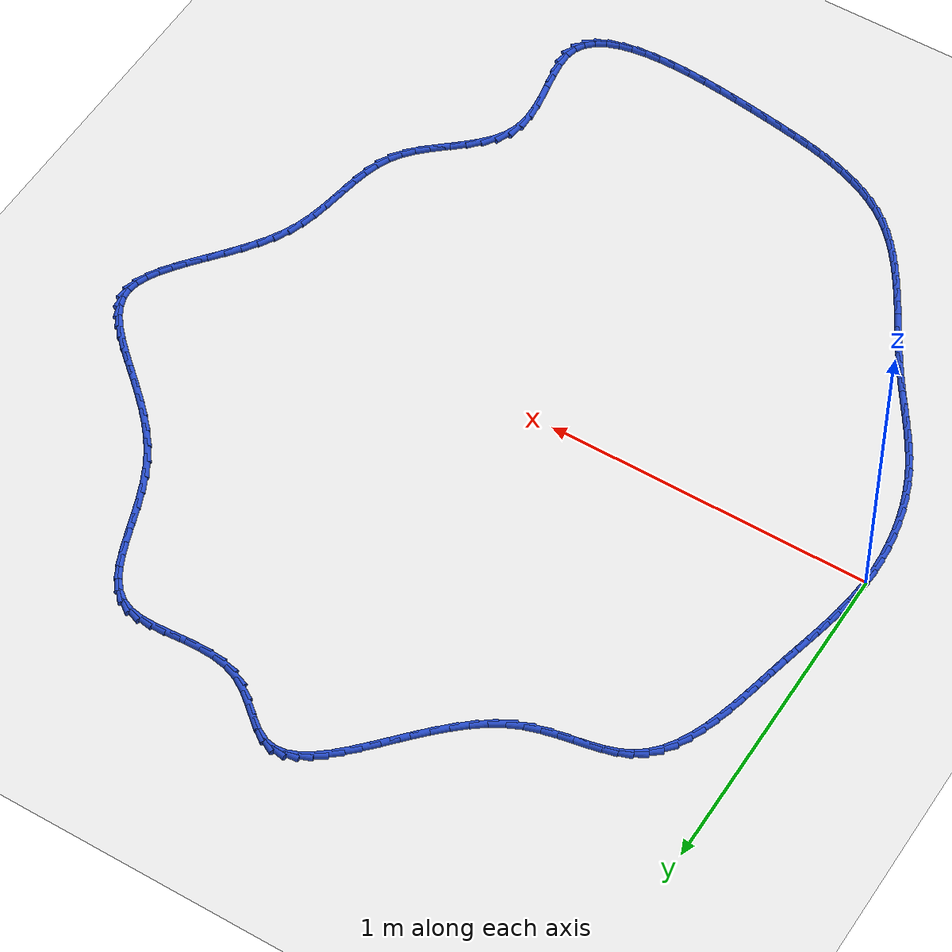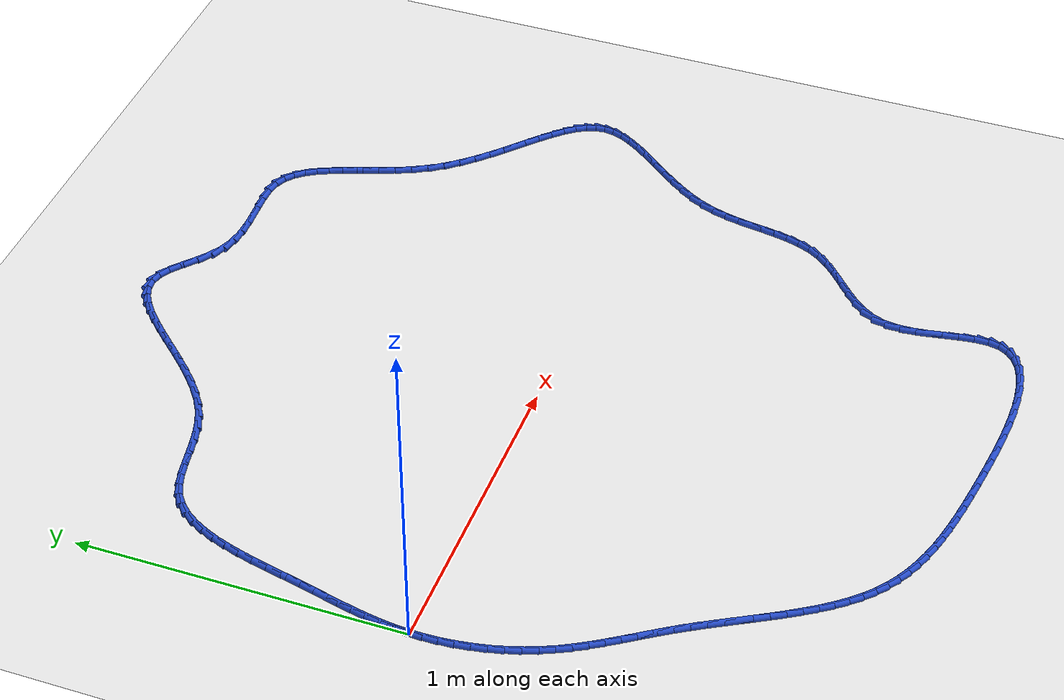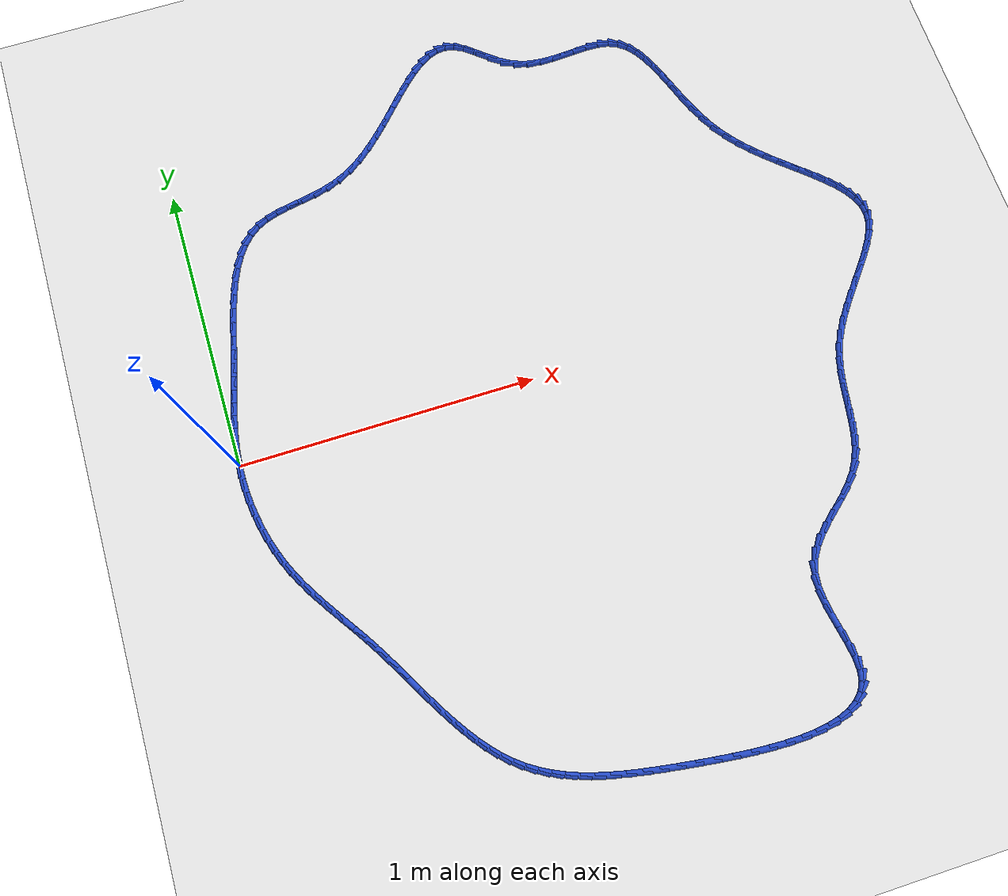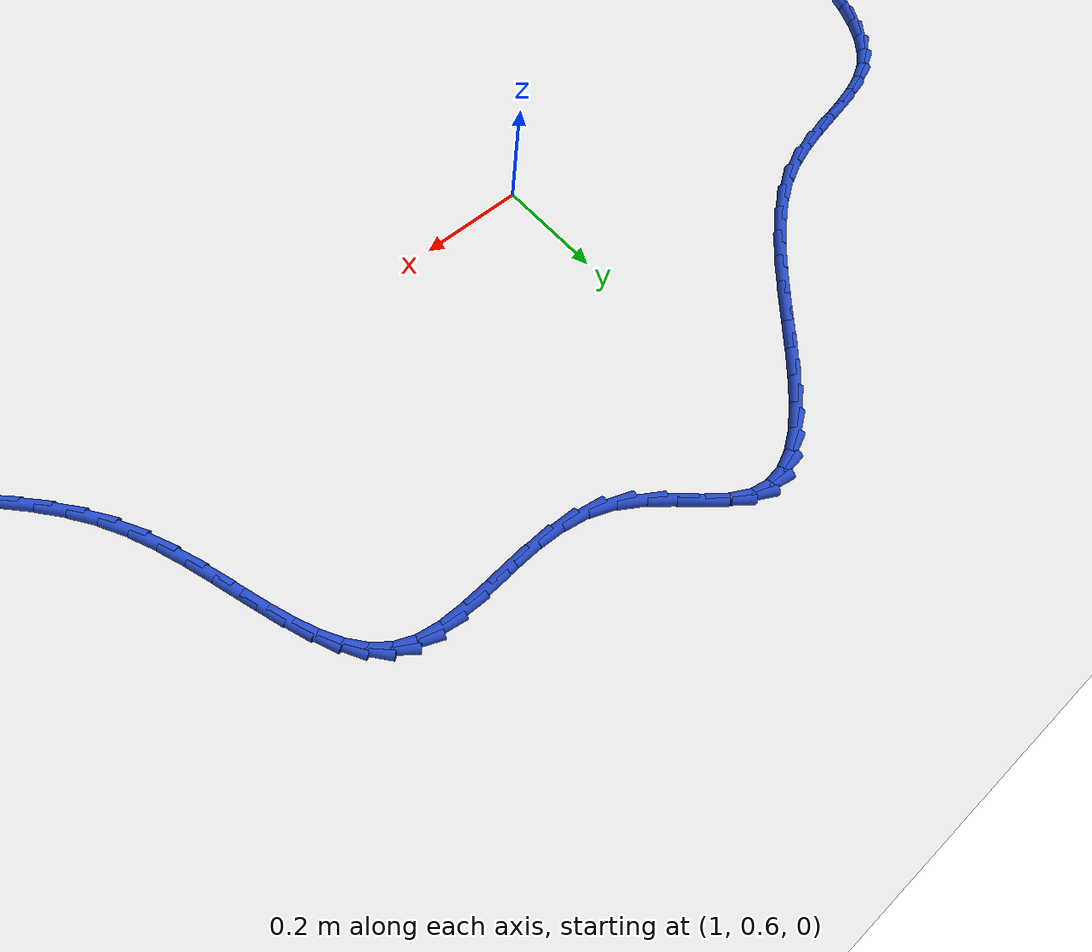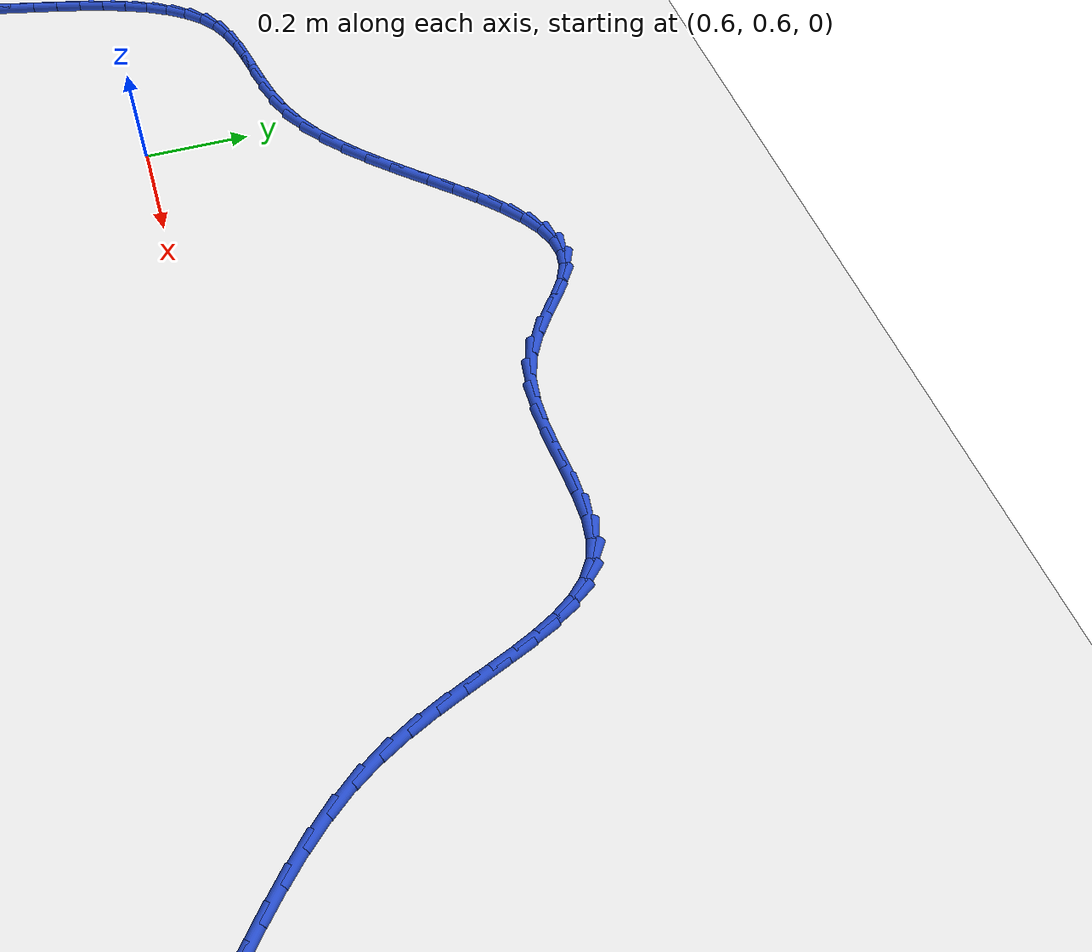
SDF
<sdf version="1.6">
 <world name="default">
  <light name="sun" type="directional">
   <pose>0 0 10 0 -0 0</pose>
   <diffuse>0.8 0.8 0.8 1</diffuse>
   <specular>0.2 0.2 0.2 1</specular>
   <attenuation>
    <range>1000</range>
    <constant>0.9</constant>
    <linear>0.01</linear>
    <quadratic>0.001</quadratic>
   </attenuation>
   <direction>-0.5 0.1 -0.9</direction>
  </light>
  <model name="ground_plane">
   <static>1</static>
   <link name="link">
    <collision name="collision">
     <geometry><plane><normal>0 0 1</normal><size>100 100</size></plane></geometry>
     <surface><friction><ode><mu>100</mu><mu2>50</mu2></ode></friction></surface>
    </collision>
    <visual name="visual">
     <cast_shadows>0</cast_shadows>
     <geometry><plane><normal>0 0 1</normal><size>100 100</size></plane></geometry>
     <material>
      <script><uri>file://media/materials/scripts/gazebo.material</uri><name>Gazebo/WhiteGlow</name></script>
     </material>
    </visual>
   </link>
  </model>
  <gravity>0 0 -9.8</gravity>
  <magnetic_field>6e-06 2.3e-05 -4.2e-05</magnetic_field>
  <atmosphere type="adiabatic"/>
  <physics name="default_physics" default="0" type="ode">
   <max_step_size>0.001</max_step_size>
   <real_time_factor>1</real_time_factor>
   <real_time_update_rate>1000</real_time_update_rate>
  </physics>
  <scene><ambient>0.4 0.4 0.4 1</ambient><background>0.7 0.7 0.7 1</background><shadows>1</shadows></scene>
  <spherical_coordinates>
   <surface_model>EARTH_WGS84</surface_model>
   <latitude_deg>0</latitude_deg>
   <longitude_deg>0</longitude_deg>
   <elevation>0</elevation>
   <heading_deg>0</heading_deg>
  </spherical_coordinates>
  <model name="line">
   <link name="link_0">
    <pose>-2.6020852139652106e-17 6.938893903907228e-17 0.01 0 1.57 1.5015367218209097</pose>
    <collision name="collision">
     <geometry><cylinder><radius>0.01</radius><length>0.08</length></cylinder></geometry>
    </collision>
    <visual name="visual">
     <material>
      <script><name>Gazebo/Blue</name><uri>file://media/materials/scripts/gazebo.material</uri></script>
     </material>
     <geometry><cylinder><radius>0.01</radius><length>0.08</length></cylinder></geometry>
    </visual>
   </link>
   <link name="link_1">
    <pose>0.0030210771628977427 0.043549844444289006 0.01 0 1.57 1.4515427963999257</pose>
    <collision name="collision">
     <geometry><cylinder><radius>0.01</radius><length>0.08</length></cylinder></geometry>
    </collision>
    <visual name="visual">
     <material>
      <script><name>Gazebo/Blue</name><uri>file://media/materials/scripts/gazebo.material</uri></script>
     </material>
     <geometry><cylinder><radius>0.01</radius><length>0.08</length></cylinder></geometry>
    </visual>
   </link>
   <link name="link_2">
    <pose>0.008180374880186836 0.0866078318617924 0.01 0 1.57 1.409806183316817</pose>
    <collision name="collision">
     <geometry><cylinder><radius>0.01</radius><length>0.08</length></cylinder></geometry>
    </collision>
    <visual name="visual">
     <material>
      <script><name>Gazebo/Blue</name><uri>file://media/materials/scripts/gazebo.material</uri></script>
     </material>
     <geometry><cylinder><radius>0.01</radius><length>0.08</length></cylinder></geometry>
    </visual>
   </link>
   <link name="link_3">
    <pose>0.015138876239396531 0.1294569198297427 0.01 0 1.57 1.3771208287644718</pose>
    <collision name="collision">
     <geometry><cylinder><radius>0.01</radius><length>0.08</length></cylinder></geometry>
    </collision>
    <visual name="visual">
     <material>
      <script><name>Gazebo/Blue</name><uri>file://media/materials/scripts/gazebo.material</uri></script>
     </material>
     <geometry><cylinder><radius>0.01</radius><length>0.08</length></cylinder></geometry>
    </visual>
   </link>
   <link name="link_4">
    <pose>0.02355756432805612 0.17238006592537258 0.01 0 1.57 1.3538444630265805</pose>
    <collision name="collision">
     <geometry><cylinder><radius>0.01</radius><length>0.08</length></cylinder></geometry>
    </collision>
    <visual name="visual">
     <material>
      <script><name>Gazebo/Blue</name><uri>file://media/materials/scripts/gazebo.material</uri></script>
     </material>
     <geometry><cylinder><radius>0.01</radius><length>0.08</length></cylinder></geometry>
    </visual>
   </link>
   <link name="link_5">
    <pose>0.03309742223369489 0.2156602277259145 0.01 0 1.57 1.3399675565499631</pose>
    <collision name="collision">
     <geometry><cylinder><radius>0.01</radius><length>0.08</length></cylinder></geometry>
    </collision>
    <visual name="visual">
     <material>
      <script><name>Gazebo/Blue</name><uri>file://media/materials/scripts/gazebo.material</uri></script>
     </material>
     <geometry><cylinder><radius>0.01</radius><length>0.08</length></cylinder></geometry>
    </visual>
   </link>
   <link name="link_6">
    <pose>0.04341943304384212 0.259580362808601 0.01 0 1.57 1.3351920761687521</pose>
    <collision name="collision">
     <geometry><cylinder><radius>0.01</radius><length>0.08</length></cylinder></geometry>
    </collision>
    <visual name="visual">
     <material>
      <script><name>Gazebo/Blue</name><uri>file://media/materials/scripts/gazebo.material</uri></script>
     </material>
     <geometry><cylinder><radius>0.01</radius><length>0.08</length></cylinder></geometry>
    </visual>
   </link>
   <link name="link_7">
    <pose>0.05418457984602708 0.3044234287506645 0.01 0 1.57 1.3390016830281561</pose>
    <collision name="collision">
     <geometry><cylinder><radius>0.01</radius><length>0.08</length></cylinder></geometry>
    </collision>
    <visual name="visual">
     <material>
      <script><name>Gazebo/Blue</name><uri>file://media/materials/scripts/gazebo.material</uri></script>
     </material>
     <geometry><cylinder><radius>0.01</radius><length>0.08</length></cylinder></geometry>
    </visual>
   </link>
   <link name="link_8">
    <pose>0.06505384572777907 0.3504723831293377 0.01 0 1.57 1.349166826581718</pose>
    <collision name="collision">
     <geometry><cylinder><radius>0.01</radius><length>0.08</length></cylinder></geometry>
    </collision>
    <visual name="visual">
     <material>
      <script><name>Gazebo/Blue</name><uri>file://media/materials/scripts/gazebo.material</uri></script>
     </material>
     <geometry><cylinder><radius>0.01</radius><length>0.08</length></cylinder></geometry>
    </visual>
   </link>
   <link name="link_9">
    <pose>0.07574800750845703 0.3979321658598631 0.01 0 1.57 1.3528844765660348</pose>
    <collision name="collision">
     <geometry><cylinder><radius>0.01</radius><length>0.08</length></cylinder></geometry>
    </collision>
    <visual name="visual">
     <material>
      <script><name>Gazebo/Blue</name><uri>file://media/materials/scripts/gazebo.material</uri></script>
     </material>
     <geometry><cylinder><radius>0.01</radius><length>0.08</length></cylinder></geometry>
    </visual>
   </link>
   <link name="link_10">
    <pose>0.08647418946112839 0.4463731404547042 0.01 0 1.57 1.3446354608060995</pose>
    <collision name="collision">
     <geometry><cylinder><radius>0.01</radius><length>0.08</length></cylinder></geometry>
    </collision>
    <visual name="visual">
     <material>
      <script><name>Gazebo/Blue</name><uri>file://media/materials/scripts/gazebo.material</uri></script>
     </material>
     <geometry><cylinder><radius>0.01</radius><length>0.08</length></cylinder></geometry>
    </visual>
   </link>
   <link name="link_11">
    <pose>0.09767618694575322 0.49505686673913185 0.01 0 1.57 1.3243201984069741</pose>
    <collision name="collision">
     <geometry><cylinder><radius>0.01</radius><length>0.08</length></cylinder></geometry>
    </collision>
    <visual name="visual">
     <material>
      <script><name>Gazebo/Blue</name><uri>file://media/materials/scripts/gazebo.material</uri></script>
     </material>
     <geometry><cylinder><radius>0.01</radius><length>0.08</length></cylinder></geometry>
    </visual>
   </link>
   <link name="link_12">
    <pose>0.1097993761367332 0.5432428419234409 0.01 0 1.57 1.2909982533041657</pose>
    <collision name="collision">
     <geometry><cylinder><radius>0.01</radius><length>0.08</length></cylinder></geometry>
    </collision>
    <visual name="visual">
     <material>
      <script><name>Gazebo/Blue</name><uri>file://media/materials/scripts/gazebo.material</uri></script>
     </material>
     <geometry><cylinder><radius>0.01</radius><length>0.08</length></cylinder></geometry>
    </visual>
   </link>
   <link name="link_13">
    <pose>0.12328913320846982 0.5901905632179254 0.01 0 1.57 1.242813594765634</pose>
    <collision name="collision">
     <geometry><cylinder><radius>0.01</radius><length>0.08</length></cylinder></geometry>
    </collision>
    <visual name="visual">
     <material>
      <script><name>Gazebo/Blue</name><uri>file://media/materials/scripts/gazebo.material</uri></script>
     </material>
     <geometry><cylinder><radius>0.01</radius><length>0.08</length></cylinder></geometry>
    </visual>
   </link>
   <link name="link_14">
    <pose>0.13859083433536465 0.6351595278328798 0.01 0 1.57 1.1769135409235503</pose>
    <collision name="collision">
     <geometry><cylinder><radius>0.01</radius><length>0.08</length></cylinder></geometry>
    </collision>
    <visual name="visual">
     <material>
      <script><name>Gazebo/Blue</name><uri>file://media/materials/scripts/gazebo.material</uri></script>
     </material>
     <geometry><cylinder><radius>0.01</radius><length>0.08</length></cylinder></geometry>
    </visual>
   </link>
   <link name="link_15">
    <pose>0.1561498556918192 0.6774092329785986 0.01 0 1.57 1.08943323458279</pose>
    <collision name="collision">
     <geometry><cylinder><radius>0.01</radius><length>0.08</length></cylinder></geometry>
    </collision>
    <visual name="visual">
     <material>
      <script><name>Gazebo/Blue</name><uri>file://media/materials/scripts/gazebo.material</uri></script>
     </material>
     <geometry><cylinder><radius>0.01</radius><length>0.08</length></cylinder></geometry>
    </visual>
   </link>
   <link name="link_16">
    <pose>0.17641157345223518 0.7161991758653767 0.01 0 1.57 0.9758210956734124</pose>
    <collision name="collision">
     <geometry><cylinder><radius>0.01</radius><length>0.08</length></cylinder></geometry>
    </collision>
    <visual name="visual">
     <material>
      <script><name>Gazebo/Blue</name><uri>file://media/materials/scripts/gazebo.material</uri></script>
     </material>
     <geometry><cylinder><radius>0.01</radius><length>0.08</length></cylinder></geometry>
    </visual>
   </link>
   <link name="link_17">
    <pose>0.19982136379101412 0.7507888537035082 0.01 0 1.57 0.8320645323728909</pose>
    <collision name="collision">
     <geometry><cylinder><radius>0.01</radius><length>0.08</length></cylinder></geometry>
    </collision>
    <visual name="visual">
     <material>
      <script><name>Gazebo/Blue</name><uri>file://media/materials/scripts/gazebo.material</uri></script>
     </material>
     <geometry><cylinder><radius>0.01</radius><length>0.08</length></cylinder></geometry>
    </visual>
   </link>
   <link name="link_18">
    <pose>0.2268246028825574 0.7804377637032877 0.01 0 1.57 0.657496976605272</pose>
    <collision name="collision">
     <geometry><cylinder><radius>0.01</radius><length>0.08</length></cylinder></geometry>
    </collision>
    <visual name="visual">
     <material>
      <script><name>Gazebo/Blue</name><uri>file://media/materials/scripts/gazebo.material</uri></script>
     </material>
     <geometry><cylinder><radius>0.01</radius><length>0.08</length></cylinder></geometry>
    </visual>
   </link>
   <link name="link_19">
    <pose>0.25786666690126686 0.8044054030750096 0.01 0 1.57 0.4671778127568607</pose>
    <collision name="collision">
     <geometry><cylinder><radius>0.01</radius><length>0.08</length></cylinder></geometry>
    </collision>
    <visual name="visual">
     <material>
      <script><name>Gazebo/Blue</name><uri>file://media/materials/scripts/gazebo.material</uri></script>
     </material>
     <geometry><cylinder><radius>0.01</radius><length>0.08</length></cylinder></geometry>
    </visual>
   </link>
   <link name="link_20">
    <pose>0.29324124276224894 0.8222490670003836 0.01 0 1.57 0.31873609881320875</pose>
    <collision name="collision">
     <geometry><cylinder><radius>0.01</radius><length>0.08</length></cylinder></geometry>
    </collision>
    <visual name="visual">
     <material>
      <script><name>Gazebo/Blue</name><uri>file://media/materials/scripts/gazebo.material</uri></script>
     </material>
     <geometry><cylinder><radius>0.01</radius><length>0.08</length></cylinder></geometry>
    </visual>
   </link>
   <link name="link_21">
    <pose>0.3324035535397463 0.8351721318146237 0.01 0 1.57 0.22797307189889215</pose>
    <collision name="collision">
     <geometry><cylinder><radius>0.01</radius><length>0.08</length></cylinder></geometry>
    </collision>
    <visual name="visual">
     <material>
      <script><name>Gazebo/Blue</name><uri>file://media/materials/scripts/gazebo.material</uri></script>
     </material>
     <geometry><cylinder><radius>0.01</radius><length>0.08</length></cylinder></geometry>
    </visual>
   </link>
   <link name="link_22">
    <pose>0.3745207193779901 0.8449435805973826 0.01 0 1.57 0.18741160357542075</pose>
    <collision name="collision">
     <geometry><cylinder><radius>0.01</radius><length>0.08</length></cylinder></geometry>
    </collision>
    <visual name="visual">
     <material>
      <script><name>Gazebo/Blue</name><uri>file://media/materials/scripts/gazebo.material</uri></script>
     </material>
     <geometry><cylinder><radius>0.01</radius><length>0.08</length></cylinder></geometry>
    </visual>
   </link>
   <link name="link_23">
    <pose>0.41875959860259976 0.8533329104334043 0.01 0 1.57 0.19044214409757504</pose>
    <collision name="collision">
     <geometry><cylinder><radius>0.01</radius><length>0.08</length></cylinder></geometry>
    </collision>
    <visual name="visual">
     <material>
      <script><name>Gazebo/Blue</name><uri>file://media/materials/scripts/gazebo.material</uri></script>
     </material>
     <geometry><cylinder><radius>0.01</radius><length>0.08</length></cylinder></geometry>
    </visual>
   </link>
   <link name="link_24">
    <pose>0.46428704953919464 0.862109618407433 0.01 0 1.57 0.2334401766750805</pose>
    <collision name="collision">
     <geometry><cylinder><radius>0.01</radius><length>0.08</length></cylinder></geometry>
    </collision>
    <visual name="visual">
     <material>
      <script><name>Gazebo/Blue</name><uri>file://media/materials/scripts/gazebo.material</uri></script>
     </material>
     <geometry><cylinder><radius>0.01</radius><length>0.08</length></cylinder></geometry>
    </visual>
   </link>
   <link name="link_25">
    <pose>0.5102699305133935 0.8730432016042121 0.01 0 1.57 0.31499081103400906</pose>
    <collision name="collision">
     <geometry><cylinder><radius>0.01</radius><length>0.08</length></cylinder></geometry>
    </collision>
    <visual name="visual">
     <material>
      <script><name>Gazebo/Blue</name><uri>file://media/materials/scripts/gazebo.material</uri></script>
     </material>
     <geometry><cylinder><radius>0.01</radius><length>0.08</length></cylinder></geometry>
    </visual>
   </link>
   <link name="link_26">
    <pose>0.5558750998508163 0.8879031571084859 0.01 0 1.57 0.4331832673419882</pose>
    <collision name="collision">
     <geometry><cylinder><radius>0.01</radius><length>0.08</length></cylinder></geometry>
    </collision>
    <visual name="visual">
     <material>
      <script><name>Gazebo/Blue</name><uri>file://media/materials/scripts/gazebo.material</uri></script>
     </material>
     <geometry><cylinder><radius>0.01</radius><length>0.08</length></cylinder></geometry>
    </visual>
   </link>
   <link name="link_27">
    <pose>0.6002761705646802 0.9084377413733784 0.01 0 1.57 0.5600879154808069</pose>
    <collision name="collision">
     <geometry><cylinder><radius>0.01</radius><length>0.08</length></cylinder></geometry>
    </collision>
    <visual name="visual">
     <material>
      <script><name>Gazebo/Blue</name><uri>file://media/materials/scripts/gazebo.material</uri></script>
     </material>
     <geometry><cylinder><radius>0.01</radius><length>0.08</length></cylinder></geometry>
    </visual>
   </link>
   <link name="link_28">
    <pose>0.643014780779613 0.9352379277498525 0.01 0 1.57 0.6596476481467995</pose>
    <collision name="collision">
     <geometry><cylinder><radius>0.01</radius><length>0.08</length></cylinder></geometry>
    </collision>
    <visual name="visual">
     <material>
      <script><name>Gazebo/Blue</name><uri>file://media/materials/scripts/gazebo.material</uri></script>
     </material>
     <geometry><cylinder><radius>0.01</radius><length>0.08</length></cylinder></geometry>
    </visual>
   </link>
   <link name="link_29">
    <pose>0.6841825581202264 0.9671652055537762 0.01 0 1.57 0.7330117037128852</pose>
    <collision name="collision">
     <geometry><cylinder><radius>0.01</radius><length>0.08</length></cylinder></geometry>
    </collision>
    <visual name="visual">
     <material>
      <script><name>Gazebo/Blue</name><uri>file://media/materials/scripts/gazebo.material</uri></script>
     </material>
     <geometry><cylinder><radius>0.01</radius><length>0.08</length></cylinder></geometry>
    </visual>
   </link>
   <link name="link_30">
    <pose>0.7239161292348578 1.0029395612302665 0.01 0 1.57 0.7841664014365014</pose>
    <collision name="collision">
     <geometry><cylinder><radius>0.01</radius><length>0.08</length></cylinder></geometry>
    </collision>
    <visual name="visual">
     <material>
      <script><name>Gazebo/Blue</name><uri>file://media/materials/scripts/gazebo.material</uri></script>
     </material>
     <geometry><cylinder><radius>0.01</radius><length>0.08</length></cylinder></geometry>
    </visual>
   </link>
   <link name="link_31">
    <pose>0.7623521207718458 1.0412809812244412 0.01 0 1.57 0.8159910181667126</pose>
    <collision name="collision">
     <geometry><cylinder><radius>0.01</radius><length>0.08</length></cylinder></geometry>
    </collision>
    <visual name="visual">
     <material>
      <script><name>Gazebo/Blue</name><uri>file://media/materials/scripts/gazebo.material</uri></script>
     </material>
     <geometry><cylinder><radius>0.01</radius><length>0.08</length></cylinder></geometry>
    </visual>
   </link>
   <link name="link_32">
    <pose>0.7996271593795277 1.0809094519814177 0.01 0 1.57 0.8299721801608987</pose>
    <collision name="collision">
     <geometry><cylinder><radius>0.01</radius><length>0.08</length></cylinder></geometry>
    </collision>
    <visual name="visual">
     <material>
      <script><name>Gazebo/Blue</name><uri>file://media/materials/scripts/gazebo.material</uri></script>
     </material>
     <geometry><cylinder><radius>0.01</radius><length>0.08</length></cylinder></geometry>
    </visual>
   </link>
   <link name="link_33">
    <pose>0.8358778717062421 1.1205449599463133 0.01 0 1.57 0.8260606718281216</pose>
    <collision name="collision">
     <geometry><cylinder><radius>0.01</radius><length>0.08</length></cylinder></geometry>
    </collision>
    <visual name="visual">
     <material>
      <script><name>Gazebo/Blue</name><uri>file://media/materials/scripts/gazebo.material</uri></script>
     </material>
     <geometry><cylinder><radius>0.01</radius><length>0.08</length></cylinder></geometry>
    </visual>
   </link>
   <link name="link_34">
    <pose>0.8712408844003261 1.158907491564246 0.01 0 1.57 0.802402727187894</pose>
    <collision name="collision">
     <geometry><cylinder><radius>0.01</radius><length>0.08</length></cylinder></geometry>
    </collision>
    <visual name="visual">
     <material>
      <script><name>Gazebo/Blue</name><uri>file://media/materials/scripts/gazebo.material</uri></script>
     </material>
     <geometry><cylinder><radius>0.01</radius><length>0.08</length></cylinder></geometry>
    </visual>
   </link>
   <link name="link_35">
    <pose>0.9058528241101184 1.1947170332803327 0.01 0 1.57 0.7547751546846299</pose>
    <collision name="collision">
     <geometry><cylinder><radius>0.01</radius><length>0.08</length></cylinder></geometry>
    </collision>
    <visual name="visual">
     <material>
      <script><name>Gazebo/Blue</name><uri>file://media/materials/scripts/gazebo.material</uri></script>
     </material>
     <geometry><cylinder><radius>0.01</radius><length>0.08</length></cylinder></geometry>
    </visual>
   </link>
   <link name="link_36">
    <pose>0.9398503174839569 1.2266935715396918 0.01 0 1.57 0.6756095453964882</pose>
    <collision name="collision">
     <geometry><cylinder><radius>0.01</radius><length>0.08</length></cylinder></geometry>
    </collision>
    <visual name="visual">
     <material>
      <script><name>Gazebo/Blue</name><uri>file://media/materials/scripts/gazebo.material</uri></script>
     </material>
     <geometry><cylinder><radius>0.01</radius><length>0.08</length></cylinder></geometry>
    </visual>
   </link>
   <link name="link_37">
    <pose>0.973369991170179 1.2535570927874395 0.01 0 1.57 0.5528120177913814</pose>
    <collision name="collision">
     <geometry><cylinder><radius>0.01</radius><length>0.08</length></cylinder></geometry>
    </collision>
    <visual name="visual">
     <material>
      <script><name>Gazebo/Blue</name><uri>file://media/materials/scripts/gazebo.material</uri></script>
     </material>
     <geometry><cylinder><radius>0.01</radius><length>0.08</length></cylinder></geometry>
    </visual>
   </link>
   <link name="link_38">
    <pose>1.0065484718171234 1.274027583468695 0.01 0 1.57 0.3702129794753879</pose>
    <collision name="collision">
     <geometry><cylinder><radius>0.01</radius><length>0.08</length></cylinder></geometry>
    </collision>
    <visual name="visual">
     <material>
      <script><name>Gazebo/Blue</name><uri>file://media/materials/scripts/gazebo.material</uri></script>
     </material>
     <geometry><cylinder><radius>0.01</radius><length>0.08</length></cylinder></geometry>
    </visual>
   </link>
   <link name="link_39">
    <pose>1.0395223860731275 1.2868250300285742 0.01 0 1.57 0.11630228064001204</pose>
    <collision name="collision">
     <geometry><cylinder><radius>0.01</radius><length>0.08</length></cylinder></geometry>
    </collision>
    <visual name="visual">
     <material>
      <script><name>Gazebo/Blue</name><uri>file://media/materials/scripts/gazebo.material</uri></script>
     </material>
     <geometry><cylinder><radius>0.01</radius><length>0.08</length></cylinder></geometry>
    </visual>
   </link>
   <link name="link_40">
    <pose>1.0724283605865295 1.290669418912195 0.01 0 1.57 -0.19137415824508225</pose>
    <collision name="collision">
     <geometry><cylinder><radius>0.01</radius><length>0.08</length></cylinder></geometry>
    </collision>
    <visual name="visual">
     <material>
      <script><name>Gazebo/Blue</name><uri>file://media/materials/scripts/gazebo.material</uri></script>
     </material>
     <geometry><cylinder><radius>0.01</radius><length>0.08</length></cylinder></geometry>
    </visual>
   </link>
   <link name="link_41">
    <pose>1.1054030220056674 1.2842807365646753 0.01 0 1.57 -0.48402177353507675</pose>
    <collision name="collision">
     <geometry><cylinder><radius>0.01</radius><length>0.08</length></cylinder></geometry>
    </collision>
    <visual name="visual">
     <material>
      <script><name>Gazebo/Blue</name><uri>file://media/materials/scripts/gazebo.material</uri></script>
     </material>
     <geometry><cylinder><radius>0.01</radius><length>0.08</length></cylinder></geometry>
    </visual>
   </link>
   <link name="link_42">
    <pose>1.1386236652736212 1.2668155343347673 0.01 0 1.57 -0.6506811001834258</pose>
    <collision name="collision">
     <geometry><cylinder><radius>0.01</radius><length>0.08</length></cylinder></geometry>
    </collision>
    <visual name="visual">
     <material>
      <script><name>Gazebo/Blue</name><uri>file://media/materials/scripts/gazebo.material</uri></script>
     </material>
     <geometry><cylinder><radius>0.01</radius><length>0.08</length></cylinder></geometry>
    </visual>
   </link>
   <link name="link_43">
    <pose>1.1725957621900112 1.240953267559664 0.01 0 1.57 -0.701161776089723</pose>
    <collision name="collision">
     <geometry><cylinder><radius>0.01</radius><length>0.08</length></cylinder></geometry>
    </collision>
    <visual name="visual">
     <material>
      <script><name>Gazebo/Blue</name><uri>file://media/materials/scripts/gazebo.material</uri></script>
     </material>
     <geometry><cylinder><radius>0.01</radius><length>0.08</length></cylinder></geometry>
    </visual>
   </link>
   <link name="link_44">
    <pose>1.2079834199008672 1.2110763059760268 0.01 0 1.57 -0.6669385789431086</pose>
    <collision name="collision">
     <geometry><cylinder><radius>0.01</radius><length>0.08</length></cylinder></geometry>
    </collision>
    <visual name="visual">
     <material>
      <script><name>Gazebo/Blue</name><uri>file://media/materials/scripts/gazebo.material</uri></script>
     </material>
     <geometry><cylinder><radius>0.01</radius><length>0.08</length></cylinder></geometry>
    </visual>
   </link>
   <link name="link_45">
    <pose>1.2454517774009268 1.1815780959819424 0.01 0 1.57 -0.5512727774426774</pose>
    <collision name="collision">
     <geometry><cylinder><radius>0.01</radius><length>0.08</length></cylinder></geometry>
    </collision>
    <visual name="visual">
     <material>
      <script><name>Gazebo/Blue</name><uri>file://media/materials/scripts/gazebo.material</uri></script>
     </material>
     <geometry><cylinder><radius>0.01</radius><length>0.08</length></cylinder></geometry>
    </visual>
   </link>
   <link name="link_46">
    <pose>1.2856659736849265 1.1568520839754979 0.01 0 1.57 -0.35522282201329924</pose>
    <collision name="collision">
     <geometry><cylinder><radius>0.01</radius><length>0.08</length></cylinder></geometry>
    </collision>
    <visual name="visual">
     <material>
      <script><name>Gazebo/Blue</name><uri>file://media/materials/scripts/gazebo.material</uri></script>
     </material>
     <geometry><cylinder><radius>0.01</radius><length>0.08</length></cylinder></geometry>
    </visual>
   </link>
   <link name="link_47">
    <pose>1.3291391229474097 1.140725345583839 0.01 0 1.57 -0.16975197883430354</pose>
    <collision name="collision">
     <geometry><cylinder><radius>0.01</radius><length>0.08</length></cylinder></geometry>
    </collision>
    <visual name="visual">
     <material>
      <script><name>Gazebo/Blue</name><uri>file://media/materials/scripts/gazebo.material</uri></script>
     </material>
     <geometry><cylinder><radius>0.01</radius><length>0.08</length></cylinder></geometry>
    </visual>
   </link>
   <link name="link_48">
    <pose>1.3752558801868564 1.1328208640490016 0.01 0 1.57 -0.04092604989559028</pose>
    <collision name="collision">
     <geometry><cylinder><radius>0.01</radius><length>0.08</length></cylinder></geometry>
    </collision>
    <visual name="visual">
     <material>
      <script><name>Gazebo/Blue</name><uri>file://media/materials/scripts/gazebo.material</uri></script>
     </material>
     <geometry><cylinder><radius>0.01</radius><length>0.08</length></cylinder></geometry>
    </visual>
   </link>
   <link name="link_49">
    <pose>1.4228931975238088 1.130870167600295 0.01 0 1.57 0.03590906795269693</pose>
    <collision name="collision">
     <geometry><cylinder><radius>0.01</radius><length>0.08</length></cylinder></geometry>
    </collision>
    <visual name="visual">
     <material>
      <script><name>Gazebo/Blue</name><uri>file://media/materials/scripts/gazebo.material</uri></script>
     </material>
     <geometry><cylinder><radius>0.01</radius><length>0.08</length></cylinder></geometry>
    </visual>
   </link>
   <link name="link_50">
    <pose>1.4709255907290666 1.1325957078079583 0.01 0 1.57 0.06595277640100475</pose>
    <collision name="collision">
     <geometry><cylinder><radius>0.01</radius><length>0.08</length></cylinder></geometry>
    </collision>
    <visual name="visual">
     <material>
      <script><name>Gazebo/Blue</name><uri>file://media/materials/scripts/gazebo.material</uri></script>
     </material>
     <geometry><cylinder><radius>0.01</radius><length>0.08</length></cylinder></geometry>
    </visual>
   </link>
   <link name="link_51">
    <pose>1.5182275755734296 1.1357199362422323 0.01 0 1.57 0.049367145772272476</pose>
    <collision name="collision">
     <geometry><cylinder><radius>0.01</radius><length>0.08</length></cylinder></geometry>
    </collision>
    <visual name="visual">
     <material>
      <script><name>Gazebo/Blue</name><uri>file://media/materials/scripts/gazebo.material</uri></script>
     </material>
     <geometry><cylinder><radius>0.01</radius><length>0.08</length></cylinder></geometry>
    </visual>
   </link>
   <link name="link_52">
    <pose>1.563673667827697 1.1379653044733562 0.01 0 1.57 -0.021450765752319714</pose>
    <collision name="collision">
     <geometry><cylinder><radius>0.01</radius><length>0.08</length></cylinder></geometry>
    </collision>
    <visual name="visual">
     <material>
      <script><name>Gazebo/Blue</name><uri>file://media/materials/scripts/gazebo.material</uri></script>
     </material>
     <geometry><cylinder><radius>0.01</radius><length>0.08</length></cylinder></geometry>
    </visual>
   </link>
   <link name="link_53">
    <pose>1.6061383832626688 1.13705426407157 0.01 0 1.57 -0.16393142986766965</pose>
    <collision name="collision">
     <geometry><cylinder><radius>0.01</radius><length>0.08</length></cylinder></geometry>
    </collision>
    <visual name="visual">
     <material>
      <script><name>Gazebo/Blue</name><uri>file://media/materials/scripts/gazebo.material</uri></script>
     </material>
     <geometry><cylinder><radius>0.01</radius><length>0.08</length></cylinder></geometry>
    </visual>
   </link>
   <link name="link_54">
    <pose>1.6444962376491437 1.1307092666071121 0.01 0 1.57 -0.39561650465453124</pose>
    <collision name="collision">
     <geometry><cylinder><radius>0.01</radius><length>0.08</length></cylinder></geometry>
    </collision>
    <visual name="visual">
     <material>
      <script><name>Gazebo/Blue</name><uri>file://media/materials/scripts/gazebo.material</uri></script>
     </material>
     <geometry><cylinder><radius>0.01</radius><length>0.08</length></cylinder></geometry>
    </visual>
   </link>
   <link name="link_55">
    <pose>1.677730837523715 1.1168293118525852 0.01 0 1.57 -0.6526398691585391</pose>
    <collision name="collision">
     <geometry><cylinder><radius>0.01</radius><length>0.08</length></cylinder></geometry>
    </collision>
    <visual name="visual">
     <material>
      <script><name>Gazebo/Blue</name><uri>file://media/materials/scripts/gazebo.material</uri></script>
     </material>
     <geometry><cylinder><radius>0.01</radius><length>0.08</length></cylinder></geometry>
    </visual>
   </link>
   <link name="link_56">
    <pose>1.706003056471231 1.0952186422430634 0.01 0 1.57 -0.8648523216458641</pose>
    <collision name="collision">
     <geometry><cylinder><radius>0.01</radius><length>0.08</length></cylinder></geometry>
    </collision>
    <visual name="visual">
     <material>
      <script><name>Gazebo/Blue</name><uri>file://media/materials/scripts/gazebo.material</uri></script>
     </material>
     <geometry><cylinder><radius>0.01</radius><length>0.08</length></cylinder></geometry>
    </visual>
   </link>
   <link name="link_57">
    <pose>1.7301922424033247 1.06684425079031 0.01 0 1.57 -1.0196173130961677</pose>
    <collision name="collision">
     <geometry><cylinder><radius>0.01</radius><length>0.08</length></cylinder></geometry>
    </collision>
    <visual name="visual">
     <material>
      <script><name>Gazebo/Blue</name><uri>file://media/materials/scripts/gazebo.material</uri></script>
     </material>
     <geometry><cylinder><radius>0.01</radius><length>0.08</length></cylinder></geometry>
    </visual>
   </link>
   <link name="link_58">
    <pose>1.751188001516777 1.032689732111085 0.01 0 1.57 -1.1233716317697025</pose>
    <collision name="collision">
     <geometry><cylinder><radius>0.01</radius><length>0.08</length></cylinder></geometry>
    </collision>
    <visual name="visual">
     <material>
      <script><name>Gazebo/Blue</name><uri>file://media/materials/scripts/gazebo.material</uri></script>
     </material>
     <geometry><cylinder><radius>0.01</radius><length>0.08</length></cylinder></geometry>
    </visual>
   </link>
   <link name="link_59">
    <pose>1.7698799400083691 0.993738680822149 0.01 0 1.57 -1.186824878893677</pose>
    <collision name="collision">
     <geometry><cylinder><radius>0.01</radius><length>0.08</length></cylinder></geometry>
    </collision>
    <visual name="visual">
     <material>
      <script><name>Gazebo/Blue</name><uri>file://media/materials/scripts/gazebo.material</uri></script>
     </material>
     <geometry><cylinder><radius>0.01</radius><length>0.08</length></cylinder></geometry>
    </visual>
   </link>
   <link name="link_60">
    <pose>1.7871576640748832 0.9509746915402617 0.01 0 1.57 -1.218664188829873</pose>
    <collision name="collision">
     <geometry><cylinder><radius>0.01</radius><length>0.08</length></cylinder></geometry>
    </collision>
    <visual name="visual">
     <material>
      <script><name>Gazebo/Blue</name><uri>file://media/materials/scripts/gazebo.material</uri></script>
     </material>
     <geometry><cylinder><radius>0.01</radius><length>0.08</length></cylinder></geometry>
    </visual>
   </link>
   <link name="link_61">
    <pose>1.8039107799131007 0.9053813588821831 0.01 0 1.57 -1.2244936698728435</pose>
    <collision name="collision">
     <geometry><cylinder><radius>0.01</radius><length>0.08</length></cylinder></geometry>
    </collision>
    <visual name="visual">
     <material>
      <script><name>Gazebo/Blue</name><uri>file://media/materials/scripts/gazebo.material</uri></script>
     </material>
     <geometry><cylinder><radius>0.01</radius><length>0.08</length></cylinder></geometry>
    </visual>
   </link>
   <link name="link_62">
    <pose>1.8210288937198025 0.8579422774646733 0.01 0 1.57 -1.2073192243812234</pose>
    <collision name="collision">
     <geometry><cylinder><radius>0.01</radius><length>0.08</length></cylinder></geometry>
    </collision>
    <visual name="visual">
     <material>
      <script><name>Gazebo/Blue</name><uri>file://media/materials/scripts/gazebo.material</uri></script>
     </material>
     <geometry><cylinder><radius>0.01</radius><length>0.08</length></cylinder></geometry>
    </visual>
   </link>
   <link name="link_63">
    <pose>1.839401611691771 0.8096410419044923 0.01 0 1.57 -1.168213626999577</pose>
    <collision name="collision">
     <geometry><cylinder><radius>0.01</radius><length>0.08</length></cylinder></geometry>
    </collision>
    <visual name="visual">
     <material>
      <script><name>Gazebo/Blue</name><uri>file://media/materials/scripts/gazebo.material</uri></script>
     </material>
     <geometry><cylinder><radius>0.01</radius><length>0.08</length></cylinder></geometry>
    </visual>
   </link>
   <link name="link_64">
    <pose>1.8599185400257874 0.761461246818401 0.01 0 1.57 -1.1069216172857308</pose>
    <collision name="collision">
     <geometry><cylinder><radius>0.01</radius><length>0.08</length></cylinder></geometry>
    </collision>
    <visual name="visual">
     <material>
      <script><name>Gazebo/Blue</name><uri>file://media/materials/scripts/gazebo.material</uri></script>
     </material>
     <geometry><cylinder><radius>0.01</radius><length>0.08</length></cylinder></geometry>
    </visual>
   </link>
   <link name="link_65">
    <pose>1.8834692849186327 0.7143864868231589 0.01 0 1.57 -1.0227232085715938</pose>
    <collision name="collision">
     <geometry><cylinder><radius>0.01</radius><length>0.08</length></cylinder></geometry>
    </collision>
    <visual name="visual">
     <material>
      <script><name>Gazebo/Blue</name><uri>file://media/materials/scripts/gazebo.material</uri></script>
     </material>
     <geometry><cylinder><radius>0.01</radius><length>0.08</length></cylinder></geometry>
    </visual>
   </link>
   <link name="link_66">
    <pose>1.9109348651779916 0.6693946631426695 0.01 0 1.57 -0.9299960899307664</pose>
    <collision name="collision">
     <geometry><cylinder><radius>0.01</radius><length>0.08</length></cylinder></geometry>
    </collision>
    <visual name="visual">
     <material>
      <script><name>Gazebo/Blue</name><uri>file://media/materials/scripts/gazebo.material</uri></script>
     </material>
     <geometry><cylinder><radius>0.01</radius><length>0.08</length></cylinder></geometry>
    </visual>
   </link>
   <link name="link_67">
    <pose>1.9425339900322058 0.6270245693064381 0.01 0 1.57 -0.8537988232908266</pose>
    <collision name="collision">
     <geometry><cylinder><radius>0.01</radius><length>0.08</length></cylinder></geometry>
    </collision>
    <visual name="visual">
     <material>
      <script><name>Gazebo/Blue</name><uri>file://media/materials/scripts/gazebo.material</uri></script>
     </material>
     <geometry><cylinder><radius>0.01</radius><length>0.08</length></cylinder></geometry>
    </visual>
   </link>
   <link name="link_68">
    <pose>1.9773638933218654 0.587071466684384 0.01 0 1.57 -0.7955944325724809</pose>
    <collision name="collision">
     <geometry><cylinder><radius>0.01</radius><length>0.08</length></cylinder></geometry>
    </collision>
    <visual name="visual">
     <material>
      <script><name>Gazebo/Blue</name><uri>file://media/materials/scripts/gazebo.material</uri></script>
     </material>
     <geometry><cylinder><radius>0.01</radius><length>0.08</length></cylinder></geometry>
    </visual>
   </link>
   <link name="link_69">
    <pose>2.014413325563045 0.5492586927848467 0.01 0 1.57 -0.7542977915984361</pose>
    <collision name="collision">
     <geometry><cylinder><radius>0.01</radius><length>0.08</length></cylinder></geometry>
    </collision>
    <visual name="visual">
     <material>
      <script><name>Gazebo/Blue</name><uri>file://media/materials/scripts/gazebo.material</uri></script>
     </material>
     <geometry><cylinder><radius>0.01</radius><length>0.08</length></cylinder></geometry>
    </visual>
   </link>
   <link name="link_70">
    <pose>2.0526710372718218 0.5133095851161652 0.01 0 1.57 -0.7292526877594063</pose>
    <collision name="collision">
     <geometry><cylinder><radius>0.01</radius><length>0.08</length></cylinder></geometry>
    </collision>
    <visual name="visual">
     <material>
      <script><name>Gazebo/Blue</name><uri>file://media/materials/scripts/gazebo.material</uri></script>
     </material>
     <geometry><cylinder><radius>0.01</radius><length>0.08</length></cylinder></geometry>
    </visual>
   </link>
   <link name="link_71">
    <pose>2.091125778964271 0.47894748118667785 0.01 0 1.57 -0.7205773587279716</pose>
    <collision name="collision">
     <geometry><cylinder><radius>0.01</radius><length>0.08</length></cylinder></geometry>
    </collision>
    <visual name="visual">
     <material>
      <script><name>Gazebo/Blue</name><uri>file://media/materials/scripts/gazebo.material</uri></script>
     </material>
     <geometry><cylinder><radius>0.01</radius><length>0.08</length></cylinder></geometry>
    </visual>
   </link>
   <link name="link_72">
    <pose>2.128766301156468 0.44589571850472454 0.01 0 1.57 -0.7294813754477617</pose>
    <collision name="collision">
     <geometry><cylinder><radius>0.01</radius><length>0.08</length></cylinder></geometry>
    </collision>
    <visual name="visual">
     <material>
      <script><name>Gazebo/Blue</name><uri>file://media/materials/scripts/gazebo.material</uri></script>
     </material>
     <geometry><cylinder><radius>0.01</radius><length>0.08</length></cylinder></geometry>
    </visual>
   </link>
   <link name="link_73">
    <pose>2.1645813543644876 0.41387763457864385 0.01 0 1.57 -0.7586722268691207</pose>
    <collision name="collision">
     <geometry><cylinder><radius>0.01</radius><length>0.08</length></cylinder></geometry>
    </collision>
    <visual name="visual">
     <material>
      <script><name>Gazebo/Blue</name><uri>file://media/materials/scripts/gazebo.material</uri></script>
     </material>
     <geometry><cylinder><radius>0.01</radius><length>0.08</length></cylinder></geometry>
    </visual>
   </link>
   <link name="link_74">
    <pose>2.1975596891044074 0.3826165669167748 0.01 0 1.57 -0.812937807755697</pose>
    <collision name="collision">
     <geometry><cylinder><radius>0.01</radius><length>0.08</length></cylinder></geometry>
    </collision>
    <visual name="visual">
     <material>
      <script><name>Gazebo/Blue</name><uri>file://media/materials/scripts/gazebo.material</uri></script>
     </material>
     <geometry><cylinder><radius>0.01</radius><length>0.08</length></cylinder></geometry>
    </visual>
   </link>
   <link name="link_75">
    <pose>2.226690055892302 0.3518358530274569 0.01 0 1.57 -0.8998652024272887</pose>
    <collision name="collision">
     <geometry><cylinder><radius>0.01</radius><length>0.08</length></cylinder></geometry>
    </collision>
    <visual name="visual">
     <material>
      <script><name>Gazebo/Blue</name><uri>file://media/materials/scripts/gazebo.material</uri></script>
     </material>
     <geometry><cylinder><radius>0.01</radius><length>0.08</length></cylinder></geometry>
    </visual>
   </link>
   <link name="link_76">
    <pose>2.250961205244247 0.32125883041902875 0.01 0 1.57 -1.0301205051774938</pose>
    <collision name="collision">
     <geometry><cylinder><radius>0.01</radius><length>0.08</length></cylinder></geometry>
    </collision>
    <visual name="visual">
     <material>
      <script><name>Gazebo/Blue</name><uri>file://media/materials/scripts/gazebo.material</uri></script>
     </material>
     <geometry><cylinder><radius>0.01</radius><length>0.08</length></cylinder></geometry>
    </visual>
   </link>
   <link name="link_77">
    <pose>2.2693618876763186 0.2906088365998292 0.01 0 1.57 -1.2150238517202032</pose>
    <collision name="collision">
     <geometry><cylinder><radius>0.01</radius><length>0.08</length></cylinder></geometry>
    </collision>
    <visual name="visual">
     <material>
      <script><name>Gazebo/Blue</name><uri>file://media/materials/scripts/gazebo.material</uri></script>
     </material>
     <geometry><cylinder><radius>0.01</radius><length>0.08</length></cylinder></geometry>
    </visual>
   </link>
   <link name="link_78">
    <pose>2.280880853704592 0.2596092090781982 0.01 0 1.57 -1.4566419993967967</pose>
    <collision name="collision">
     <geometry><cylinder><radius>0.01</radius><length>0.08</length></cylinder></geometry>
    </collision>
    <visual name="visual">
     <material>
      <script><name>Gazebo/Blue</name><uri>file://media/materials/scripts/gazebo.material</uri></script>
     </material>
     <geometry><cylinder><radius>0.01</radius><length>0.08</length></cylinder></geometry>
    </visual>
   </link>
   <link name="link_79">
    <pose>2.2845068538451425 0.2279832853624737 0.01 0 1.57 1.4210609078903966</pose>
    <collision name="collision">
     <geometry><cylinder><radius>0.01</radius><length>0.08</length></cylinder></geometry>
    </collision>
    <visual name="visual">
     <material>
      <script><name>Gazebo/Blue</name><uri>file://media/materials/scripts/gazebo.material</uri></script>
     </material>
     <geometry><cylinder><radius>0.01</radius><length>0.08</length></cylinder></geometry>
    </visual>
   </link>
   <link name="link_80">
    <pose>2.2796056824183935 0.19549606643556613 0.01 0 1.57 1.2117868378850905</pose>
    <collision name="collision">
     <geometry><cylinder><radius>0.01</radius><length>0.08</length></cylinder></geometry>
    </collision>
    <visual name="visual">
     <material>
      <script><name>Gazebo/Blue</name><uri>file://media/materials/scripts/gazebo.material</uri></script>
     </material>
     <geometry><cylinder><radius>0.01</radius><length>0.08</length></cylinder></geometry>
    </visual>
   </link>
   <link name="link_81">
    <pose>2.267065859941414 0.16208081506705374 0.01 0 1.57 1.0678761299139456</pose>
    <collision name="collision">
     <geometry><cylinder><radius>0.01</radius><length>0.08</length></cylinder></geometry>
    </collision>
    <visual name="visual">
     <material>
      <script><name>Gazebo/Blue</name><uri>file://media/materials/scripts/gazebo.material</uri></script>
     </material>
     <geometry><cylinder><radius>0.01</radius><length>0.08</length></cylinder></geometry>
    </visual>
   </link>
   <link name="link_82">
    <pose>2.2481602612536737 0.1277132653159317 0.01 0 1.57 0.974306764942886</pose>
    <collision name="collision">
     <geometry><cylinder><radius>0.01</radius><length>0.08</length></cylinder></geometry>
    </collision>
    <visual name="visual">
     <material>
      <script><name>Gazebo/Blue</name><uri>file://media/materials/scripts/gazebo.material</uri></script>
     </material>
     <geometry><cylinder><radius>0.01</radius><length>0.08</length></cylinder></geometry>
    </visual>
   </link>
   <link name="link_83">
    <pose>2.2241617612071183 0.09236915124257525 0.01 0 1.57 0.9175100092535012</pose>
    <collision name="collision">
     <geometry><cylinder><radius>0.01</radius><length>0.08</length></cylinder></geometry>
    </collision>
    <visual name="visual">
     <material>
      <script><name>Gazebo/Blue</name><uri>file://media/materials/scripts/gazebo.material</uri></script>
     </material>
     <geometry><cylinder><radius>0.01</radius><length>0.08</length></cylinder></geometry>
    </visual>
   </link>
   <link name="link_84">
    <pose>2.1963432346536984 0.056024206907358376 0.01 0 1.57 0.8884391499865167</pose>
    <collision name="collision">
     <geometry><cylinder><radius>0.01</radius><length>0.08</length></cylinder></geometry>
    </collision>
    <visual name="visual">
     <material>
      <script><name>Gazebo/Blue</name><uri>file://media/materials/scripts/gazebo.material</uri></script>
     </material>
     <geometry><cylinder><radius>0.01</radius><length>0.08</length></cylinder></geometry>
    </visual>
   </link>
   <link name="link_85">
    <pose>2.165977556445361 0.018654166370656342 0.01 0 1.57 0.8818650069336795</pose>
    <collision name="collision">
     <geometry><cylinder><radius>0.01</radius><length>0.08</length></cylinder></geometry>
    </collision>
    <visual name="visual">
     <material>
      <script><name>Gazebo/Blue</name><uri>file://media/materials/scripts/gazebo.material</uri></script>
     </material>
     <geometry><cylinder><radius>0.01</radius><length>0.08</length></cylinder></geometry>
    </visual>
   </link>
   <link name="link_86">
    <pose>2.1343376014340554 -0.019765236307156576 0.01 0 1.57 0.8953311883080695</pose>
    <collision name="collision">
     <geometry><cylinder><radius>0.01</radius><length>0.08</length></cylinder></geometry>
    </collision>
    <visual name="visual">
     <material>
      <script><name>Gazebo/Blue</name><uri>file://media/materials/scripts/gazebo.material</uri></script>
     </material>
     <geometry><cylinder><radius>0.01</radius><length>0.08</length></cylinder></geometry>
    </visual>
   </link>
   <link name="link_87">
    <pose>2.102696244471729 -0.059258267065705715 0.01 0 1.57 0.9284520968561958</pose>
    <collision name="collision">
     <geometry><cylinder><radius>0.01</radius><length>0.08</length></cylinder></geometry>
    </collision>
    <visual name="visual">
     <material>
      <script><name>Gazebo/Blue</name><uri>file://media/materials/scripts/gazebo.material</uri></script>
     </material>
     <geometry><cylinder><radius>0.01</radius><length>0.08</length></cylinder></geometry>
    </visual>
   </link>
   <link name="link_88">
    <pose>2.072326360410331 -0.09984919184461644 0.01 0 1.57 0.9825147290813121</pose>
    <collision name="collision">
     <geometry><cylinder><radius>0.01</radius><length>0.08</length></cylinder></geometry>
    </collision>
    <visual name="visual">
     <material>
      <script><name>Gazebo/Blue</name><uri>file://media/materials/scripts/gazebo.material</uri></script>
     </material>
     <geometry><cylinder><radius>0.01</radius><length>0.08</length></cylinder></geometry>
    </visual>
   </link>
   <link name="link_89">
    <pose>2.0445008241018092 -0.141562276583515 0.01 0 1.57 1.0601838977906153</pose>
    <collision name="collision">
     <geometry><cylinder><radius>0.01</radius><length>0.08</length></cylinder></geometry>
    </collision>
    <visual name="visual">
     <material>
      <script><name>Gazebo/Blue</name><uri>file://media/materials/scripts/gazebo.material</uri></script>
     </material>
     <geometry><cylinder><radius>0.01</radius><length>0.08</length></cylinder></geometry>
    </visual>
   </link>
   <link name="link_90">
    <pose>2.020492510398112 -0.18442178722202515 0.01 0 1.57 1.1635988617889739</pose>
    <collision name="collision">
     <geometry><cylinder><radius>0.01</radius><length>0.08</length></cylinder></geometry>
    </collision>
    <visual name="visual">
     <material>
      <script><name>Gazebo/Blue</name><uri>file://media/materials/scripts/gazebo.material</uri></script>
     </material>
     <geometry><cylinder><radius>0.01</radius><length>0.08</length></cylinder></geometry>
    </visual>
   </link>
   <link name="link_91">
    <pose>2.0015073615350767 -0.22843988006481394 0.01 0 1.57 1.2675174536357787</pose>
    <collision name="collision">
     <geometry><cylinder><radius>0.01</radius><length>0.08</length></cylinder></geometry>
    </collision>
    <visual name="visual">
     <material>
      <script><name>Gazebo/Blue</name><uri>file://media/materials/scripts/gazebo.material</uri></script>
     </material>
     <geometry><cylinder><radius>0.01</radius><length>0.08</length></cylinder></geometry>
    </visual>
   </link>
   <link name="link_92">
    <pose>1.9874405190904356 -0.2733915577178625 0.01 0 1.57 1.3448038288837534</pose>
    <collision name="collision">
     <geometry><cylinder><radius>0.01</radius><length>0.08</length></cylinder></geometry>
    </collision>
    <visual name="visual">
     <material>
      <script><name>Gazebo/Blue</name><uri>file://media/materials/scripts/gazebo.material</uri></script>
     </material>
     <geometry><cylinder><radius>0.01</radius><length>0.08</length></cylinder></geometry>
    </visual>
   </link>
   <link name="link_93">
    <pose>1.976992020223422 -0.31883560117373483 0.01 0 1.57 1.3929985538239018</pose>
    <collision name="collision">
     <geometry><cylinder><radius>0.01</radius><length>0.08</length></cylinder></geometry>
    </collision>
    <visual name="visual">
     <material>
      <script><name>Gazebo/Blue</name><uri>file://media/materials/scripts/gazebo.material</uri></script>
     </material>
     <geometry><cylinder><radius>0.01</radius><length>0.08</length></cylinder></geometry>
    </visual>
   </link>
   <link name="link_94">
    <pose>1.9688181706790948 -0.3643228794159841 0.01 0 1.57 1.4114950180663197</pose>
    <collision name="collision">
     <geometry><cylinder><radius>0.01</radius><length>0.08</length></cylinder></geometry>
    </collision>
    <visual name="visual">
     <material>
      <script><name>Gazebo/Blue</name><uri>file://media/materials/scripts/gazebo.material</uri></script>
     </material>
     <geometry><cylinder><radius>0.01</radius><length>0.08</length></cylinder></geometry>
    </visual>
   </link>
   <link name="link_95">
    <pose>1.9615752762025158 -0.40940426142816094 0.01 0 1.57 1.3993936607827153</pose>
    <collision name="collision">
     <geometry><cylinder><radius>0.01</radius><length>0.08</length></cylinder></geometry>
    </collision>
    <visual name="visual">
     <material>
      <script><name>Gazebo/Blue</name><uri>file://media/materials/scripts/gazebo.material</uri></script>
     </material>
     <geometry><cylinder><radius>0.01</radius><length>0.08</length></cylinder></geometry>
    </visual>
   </link>
   <link name="link_96">
    <pose>1.9539196425387455 -0.45363061619381856 0.01 0 1.57 1.3549309332881538</pose>
    <collision name="collision">
     <geometry><cylinder><radius>0.01</radius><length>0.08</length></cylinder></geometry>
    </collision>
    <visual name="visual">
     <material>
      <script><name>Gazebo/Blue</name><uri>file://media/materials/scripts/gazebo.material</uri></script>
     </material>
     <geometry><cylinder><radius>0.01</radius><length>0.08</length></cylinder></geometry>
    </visual>
   </link>
   <link name="link_97">
    <pose>1.944507575432843 -0.4965528126965091 0.01 0 1.57 1.2757439687613161</pose>
    <collision name="collision">
     <geometry><cylinder><radius>0.01</radius><length>0.08</length></cylinder></geometry>
    </collision>
    <visual name="visual">
     <material>
      <script><name>Gazebo/Blue</name><uri>file://media/materials/scripts/gazebo.material</uri></script>
     </material>
     <geometry><cylinder><radius>0.01</radius><length>0.08</length></cylinder></geometry>
    </visual>
   </link>
   <link name="link_98">
    <pose>1.9319953806298693 -0.5377217199197849 0.01 0 1.57 1.1603654402708465</pose>
    <collision name="collision">
     <geometry><cylinder><radius>0.01</radius><length>0.08</length></cylinder></geometry>
    </collision>
    <visual name="visual">
     <material>
      <script><name>Gazebo/Blue</name><uri>file://media/materials/scripts/gazebo.material</uri></script>
     </material>
     <geometry><cylinder><radius>0.01</radius><length>0.08</length></cylinder></geometry>
    </visual>
   </link>
   <link name="link_99">
    <pose>1.9150393638748846 -0.576688206847199 0.01 0 1.57 1.011336479502829</pose>
    <collision name="collision">
     <geometry><cylinder><radius>0.01</radius><length>0.08</length></cylinder></geometry>
    </collision>
    <visual name="visual">
     <material>
      <script><name>Gazebo/Blue</name><uri>file://media/materials/scripts/gazebo.material</uri></script>
     </material>
     <geometry><cylinder><radius>0.01</radius><length>0.08</length></cylinder></geometry>
    </visual>
   </link>
   <link name="link_100">
    <pose>1.8922984054253866 -0.6130041693543725 0.01 0 1.57 0.8590803211666804</pose>
    <collision name="collision">
     <geometry><cylinder><radius>0.01</radius><length>0.08</length></cylinder></geometry>
    </collision>
    <visual name="visual">
     <material>
      <script><name>Gazebo/Blue</name><uri>file://media/materials/scripts/gazebo.material</uri></script>
     </material>
     <geometry><cylinder><radius>0.01</radius><length>0.08</length></cylinder></geometry>
    </visual>
   </link>
   <link name="link_101">
    <pose>1.863336505899754 -0.6465825273725457 0.01 0 1.57 0.7586334285078412</pose>
    <collision name="collision">
     <geometry><cylinder><radius>0.01</radius><length>0.08</length></cylinder></geometry>
    </collision>
    <visual name="visual">
     <material>
      <script><name>Gazebo/Blue</name><uri>file://media/materials/scripts/gazebo.material</uri></script>
     </material>
     <geometry><cylinder><radius>0.01</radius><length>0.08</length></cylinder></geometry>
    </visual>
   </link>
   <link name="link_102">
    <pose>1.829951072047174 -0.6782270363218417 0.01 0 1.57 0.7097951012265357</pose>
    <collision name="collision">
     <geometry><cylinder><radius>0.01</radius><length>0.08</length></cylinder></geometry>
    </collision>
    <visual name="visual">
     <material>
      <script><name>Gazebo/Blue</name><uri>file://media/materials/scripts/gazebo.material</uri></script>
     </material>
     <geometry><cylinder><radius>0.01</radius><length>0.08</length></cylinder></geometry>
    </visual>
   </link>
   <link name="link_103">
    <pose>1.794277914717638 -0.7088764303790102 0.01 0 1.57 0.7067859229128425</pose>
    <collision name="collision">
     <geometry><cylinder><radius>0.01</radius><length>0.08</length></cylinder></geometry>
    </collision>
    <visual name="visual">
     <material>
      <script><name>Gazebo/Blue</name><uri>file://media/materials/scripts/gazebo.material</uri></script>
     </material>
     <geometry><cylinder><radius>0.01</radius><length>0.08</length></cylinder></geometry>
    </visual>
   </link>
   <link name="link_104">
    <pose>1.7584528447611365 -0.7394694437208021 0.01 0 1.57 0.7491933796678254</pose>
    <collision name="collision">
     <geometry><cylinder><radius>0.01</radius><length>0.08</length></cylinder></geometry>
    </collision>
    <visual name="visual">
     <material>
      <script><name>Gazebo/Blue</name><uri>file://media/materials/scripts/gazebo.material</uri></script>
     </material>
     <geometry><cylinder><radius>0.01</radius><length>0.08</length></cylinder></geometry>
    </visual>
   </link>
   <link name="link_105">
    <pose>1.724611673027663 -0.7709448105239666 0.01 0 1.57 0.8420671908961838</pose>
    <collision name="collision">
     <geometry><cylinder><radius>0.01</radius><length>0.08</length></cylinder></geometry>
    </collision>
    <visual name="visual">
     <material>
      <script><name>Gazebo/Blue</name><uri>file://media/materials/scripts/gazebo.material</uri></script>
     </material>
     <geometry><cylinder><radius>0.01</radius><length>0.08</length></cylinder></geometry>
    </visual>
   </link>
   <link name="link_106">
    <pose>1.6948902103672083 -0.8042412649652545 0.01 0 1.57 0.9938488267173299</pose>
    <collision name="collision">
     <geometry><cylinder><radius>0.01</radius><length>0.08</length></cylinder></geometry>
    </collision>
    <visual name="visual">
     <material>
      <script><name>Gazebo/Blue</name><uri>file://media/materials/scripts/gazebo.material</uri></script>
     </material>
     <geometry><cylinder><radius>0.01</radius><length>0.08</length></cylinder></geometry>
    </visual>
   </link>
   <link name="link_107">
    <pose>1.671424267629764 -0.8402975412214159 0.01 0 1.57 1.208236156728852</pose>
    <collision name="collision">
     <geometry><cylinder><radius>0.01</radius><length>0.08</length></cylinder></geometry>
    </collision>
    <visual name="visual">
     <material>
      <script><name>Gazebo/Blue</name><uri>file://media/materials/scripts/gazebo.material</uri></script>
     </material>
     <geometry><cylinder><radius>0.01</radius><length>0.08</length></cylinder></geometry>
    </visual>
   </link>
   <link name="link_108">
    <pose>1.6563450074758224 -0.8800500443093544 0.01 0 1.57 1.438730580906716</pose>
    <collision name="collision">
     <geometry><cylinder><radius>0.01</radius><length>0.08</length></cylinder></geometry>
    </collision>
    <visual name="visual">
     <material>
      <script><name>Gazebo/Blue</name><uri>file://media/materials/scripts/gazebo.material</uri></script>
     </material>
     <geometry><cylinder><radius>0.01</radius><length>0.08</length></cylinder></geometry>
    </visual>
   </link>
   <link name="link_109">
    <pose>1.650532229117086 -0.9238081339203218 0.01 0 1.57 -1.5408060649136766</pose>
    <collision name="collision">
     <geometry><cylinder><radius>0.01</radius><length>0.08</length></cylinder></geometry>
    </collision>
    <visual name="visual">
     <material>
      <script><name>Gazebo/Blue</name><uri>file://media/materials/scripts/gazebo.material</uri></script>
     </material>
     <geometry><cylinder><radius>0.01</radius><length>0.08</length></cylinder></geometry>
    </visual>
   </link>
   <link name="link_110">
    <pose>1.6519302574589394 -0.9704102338283278 0.01 0 1.57 -1.4439127112153773</pose>
    <collision name="collision">
     <geometry><cylinder><radius>0.01</radius><length>0.08</length></cylinder></geometry>
    </collision>
    <visual name="visual">
     <material>
      <script><name>Gazebo/Blue</name><uri>file://media/materials/scripts/gazebo.material</uri></script>
     </material>
     <geometry><cylinder><radius>0.01</radius><length>0.08</length></cylinder></geometry>
    </visual>
   </link>
   <link name="link_111">
    <pose>1.6580629894529015 -1.0184840956932948 0.01 0 1.57 -1.3983364508978755</pose>
    <collision name="collision">
     <geometry><cylinder><radius>0.01</radius><length>0.08</length></cylinder></geometry>
    </collision>
    <visual name="visual">
     <material>
      <script><name>Gazebo/Blue</name><uri>file://media/materials/scripts/gazebo.material</uri></script>
     </material>
     <geometry><cylinder><radius>0.01</radius><length>0.08</length></cylinder></geometry>
    </visual>
   </link>
   <link name="link_112">
    <pose>1.6664543220504917 -1.0666574711751486 0.01 0 1.57 -1.398249630607257</pose>
    <collision name="collision">
     <geometry><cylinder><radius>0.01</radius><length>0.08</length></cylinder></geometry>
    </collision>
    <visual name="visual">
     <material>
      <script><name>Gazebo/Blue</name><uri>file://media/materials/scripts/gazebo.material</uri></script>
     </material>
     <geometry><cylinder><radius>0.01</radius><length>0.08</length></cylinder></geometry>
    </visual>
   </link>
   <link name="link_113">
    <pose>1.6746281522032302 -1.1135581119338138 0.01 0 1.57 -1.4475924613147018</pose>
    <collision name="collision">
     <geometry><cylinder><radius>0.01</radius><length>0.08</length></cylinder></geometry>
    </collision>
    <visual name="visual">
     <material>
      <script><name>Gazebo/Blue</name><uri>file://media/materials/scripts/gazebo.material</uri></script>
     </material>
     <geometry><cylinder><radius>0.01</radius><length>0.08</length></cylinder></geometry>
    </visual>
   </link>
   <link name="link_114">
    <pose>1.6801083768626348 -1.1578137696292146 0.01 0 1.57 -1.563079574858625</pose>
    <collision name="collision">
     <geometry><cylinder><radius>0.01</radius><length>0.08</length></cylinder></geometry>
    </collision>
    <visual name="visual">
     <material>
      <script><name>Gazebo/Blue</name><uri>file://media/materials/scripts/gazebo.material</uri></script>
     </material>
     <geometry><cylinder><radius>0.01</radius><length>0.08</length></cylinder></geometry>
    </visual>
   </link>
   <link name="link_115">
    <pose>1.680418892980226 -1.1980521959212769 0.01 0 1.57 1.3642914197493297</pose>
    <collision name="collision">
     <geometry><cylinder><radius>0.01</radius><length>0.08</length></cylinder></geometry>
    </collision>
    <visual name="visual">
     <material>
      <script><name>Gazebo/Blue</name><uri>file://media/materials/scripts/gazebo.material</uri></script>
     </material>
     <geometry><cylinder><radius>0.01</radius><length>0.08</length></cylinder></geometry>
    </visual>
   </link>
   <link name="link_116">
    <pose>1.6731147437970006 -1.2329183218089699 0.01 0 1.57 1.0642983695668267</pose>
    <collision name="collision">
     <geometry><cylinder><radius>0.01</radius><length>0.08</length></cylinder></geometry>
    </collision>
    <visual name="visual">
     <material>
      <script><name>Gazebo/Blue</name><uri>file://media/materials/scripts/gazebo.material</uri></script>
     </material>
     <geometry><cylinder><radius>0.01</radius><length>0.08</length></cylinder></geometry>
    </visual>
   </link>
   <link name="link_117">
    <pose>1.657093425538519 -1.2617975342288195 0.01 0 1.57 0.7699015739525611</pose>
    <collision name="collision">
     <geometry><cylinder><radius>0.01</radius><length>0.08</length></cylinder></geometry>
    </collision>
    <visual name="visual">
     <material>
      <script><name>Gazebo/Blue</name><uri>file://media/materials/scripts/gazebo.material</uri></script>
     </material>
     <geometry><cylinder><radius>0.01</radius><length>0.08</length></cylinder></geometry>
    </visual>
   </link>
   <link name="link_118">
    <pose>1.6330765534757845 -1.285081348297282 0.01 0 1.57 0.5274724385098474</pose>
    <collision name="collision">
     <geometry><cylinder><radius>0.01</radius><length>0.08</length></cylinder></geometry>
    </collision>
    <visual name="visual">
     <material>
      <script><name>Gazebo/Blue</name><uri>file://media/materials/scripts/gazebo.material</uri></script>
     </material>
     <geometry><cylinder><radius>0.01</radius><length>0.08</length></cylinder></geometry>
    </visual>
   </link>
   <link name="link_119">
    <pose>1.6019160700647395 -1.303233163613192 0.01 0 1.57 0.3455660124782833</pose>
    <collision name="collision">
     <geometry><cylinder><radius>0.01</radius><length>0.08</length></cylinder></geometry>
    </collision>
    <visual name="visual">
     <material>
      <script><name>Gazebo/Blue</name><uri>file://media/materials/scripts/gazebo.material</uri></script>
     </material>
     <geometry><cylinder><radius>0.01</radius><length>0.08</length></cylinder></geometry>
    </visual>
   </link>
   <link name="link_120">
    <pose>1.5644639177613289 -1.316716379775385 0.01 0 1.57 0.2130295983115131</pose>
    <collision name="collision">
     <geometry><cylinder><radius>0.01</radius><length>0.08</length></cylinder></geometry>
    </collision>
    <visual name="visual">
     <material>
      <script><name>Gazebo/Blue</name><uri>file://media/materials/scripts/gazebo.material</uri></script>
     </material>
     <geometry><cylinder><radius>0.01</radius><length>0.08</length></cylinder></geometry>
    </visual>
   </link>
   <link name="link_121">
    <pose>1.521572039021496 -1.3259943963826974 0.01 0 1.57 0.11607768304004415</pose>
    <collision name="collision">
     <geometry><cylinder><radius>0.01</radius><length>0.08</length></cylinder></geometry>
    </collision>
    <visual name="visual">
     <material>
      <script><name>Gazebo/Blue</name><uri>file://media/materials/scripts/gazebo.material</uri></script>
     </material>
     <geometry><cylinder><radius>0.01</radius><length>0.08</length></cylinder></geometry>
    </visual>
   </link>
   <link name="link_122">
    <pose>1.4740923763011873 -1.3315306130339646 0.01 0 1.57 0.044056099346701905</pose>
    <collision name="collision">
     <geometry><cylinder><radius>0.01</radius><length>0.08</length></cylinder></geometry>
    </collision>
    <visual name="visual">
     <material>
      <script><name>Gazebo/Blue</name><uri>file://media/materials/scripts/gazebo.material</uri></script>
     </material>
     <geometry><cylinder><radius>0.01</radius><length>0.08</length></cylinder></geometry>
    </visual>
   </link>
   <link name="link_123">
    <pose>1.4228768720563454 -1.3337884293280213 0.01 0 1.57 -0.010298907757420917</pose>
    <collision name="collision">
     <geometry><cylinder><radius>0.01</radius><length>0.08</length></cylinder></geometry>
    </collision>
    <visual name="visual">
     <material>
      <script><name>Gazebo/Blue</name><uri>file://media/materials/scripts/gazebo.material</uri></script>
     </material>
     <geometry><cylinder><radius>0.01</radius><length>0.08</length></cylinder></geometry>
    </visual>
   </link>
   <link name="link_124">
    <pose>1.368777468742915 -1.3332312448637043 0.01 0 1.57 -0.051774730634102574</pose>
    <collision name="collision">
     <geometry><cylinder><radius>0.01</radius><length>0.08</length></cylinder></geometry>
    </collision>
    <visual name="visual">
     <material>
      <script><name>Gazebo/Blue</name><uri>file://media/materials/scripts/gazebo.material</uri></script>
     </material>
     <geometry><cylinder><radius>0.01</radius><length>0.08</length></cylinder></geometry>
    </visual>
   </link>
   <link name="link_125">
    <pose>1.3126461088168402 -1.330322459239848 0.01 0 1.57 -0.08350579494485845</pose>
    <collision name="collision">
     <geometry><cylinder><radius>0.01</radius><length>0.08</length></cylinder></geometry>
    </collision>
    <visual name="visual">
     <material>
      <script><name>Gazebo/Blue</name><uri>file://media/materials/scripts/gazebo.material</uri></script>
     </material>
     <geometry><cylinder><radius>0.01</radius><length>0.08</length></cylinder></geometry>
    </visual>
   </link>
   <link name="link_126">
    <pose>1.2553347347340638 -1.325525472055289 0.01 0 1.57 -0.1075269150454504</pose>
    <collision name="collision">
     <geometry><cylinder><radius>0.01</radius><length>0.08</length></cylinder></geometry>
    </collision>
    <visual name="visual">
     <material>
      <script><name>Gazebo/Blue</name><uri>file://media/materials/scripts/gazebo.material</uri></script>
     </material>
     <geometry><cylinder><radius>0.01</radius><length>0.08</length></cylinder></geometry>
    </visual>
   </link>
   <link name="link_127">
    <pose>1.1976952889505328 -1.3193036829088625 0.01 0 1.57 -0.1251090370067884</pose>
    <collision name="collision">
     <geometry><cylinder><radius>0.01</radius><length>0.08</length></cylinder></geometry>
    </collision>
    <visual name="visual">
     <material>
      <script><name>Gazebo/Blue</name><uri>file://media/materials/scripts/gazebo.material</uri></script>
     </material>
     <geometry><cylinder><radius>0.01</radius><length>0.08</length></cylinder></geometry>
    </visual>
   </link>
   <link name="link_128">
    <pose>1.1405797139221898 -1.312120491399404 0.01 0 1.57 -0.1369423023924029</pose>
    <collision name="collision">
     <geometry><cylinder><radius>0.01</radius><length>0.08</length></cylinder></geometry>
    </collision>
    <visual name="visual">
     <material>
      <script><name>Gazebo/Blue</name><uri>file://media/materials/scripts/gazebo.material</uri></script>
     </material>
     <geometry><cylinder><radius>0.01</radius><length>0.08</length></cylinder></geometry>
    </visual>
   </link>
   <link name="link_129">
    <pose>1.0848399325651483 -1.3044392815281096 0.01 0 1.57 -0.145244804502595</pose>
    <collision name="collision">
     <geometry><cylinder><radius>0.01</radius><length>0.08</length></cylinder></geometry>
    </collision>
    <visual name="visual">
     <material>
      <script><name>Gazebo/Blue</name><uri>file://media/materials/scripts/gazebo.material</uri></script>
     </material>
     <geometry><cylinder><radius>0.01</radius><length>0.08</length></cylinder></geometry>
    </visual>
   </link>
   <link name="link_130">
    <pose>1.0311566559065553 -1.2965867676714085 0.01 0 1.57 -0.15716049957428263</pose>
    <collision name="collision">
     <geometry><cylinder><radius>0.01</radius><length>0.08</length></cylinder></geometry>
    </collision>
    <visual name="visual">
     <material>
      <script><name>Gazebo/Blue</name><uri>file://media/materials/scripts/gazebo.material</uri></script>
     </material>
     <geometry><cylinder><radius>0.01</radius><length>0.08</length></cylinder></geometry>
    </visual>
   </link>
   <link name="link_131">
    <pose>0.9796226077262568 -1.288420304297717 0.01 0 1.57 -0.17472861156729103</pose>
    <collision name="collision">
     <geometry><cylinder><radius>0.01</radius><length>0.08</length></cylinder></geometry>
    </collision>
    <visual name="visual">
     <material>
      <script><name>Gazebo/Blue</name><uri>file://media/materials/scripts/gazebo.material</uri></script>
     </material>
     <geometry><cylinder><radius>0.01</radius><length>0.08</length></cylinder></geometry>
    </visual>
   </link>
   <link name="link_132">
    <pose>0.9302043873472693 -1.2796965672234408 0.01 0 1.57 -0.19855671978430212</pose>
    <collision name="collision">
     <geometry><cylinder><radius>0.01</radius><length>0.08</length></cylinder></geometry>
    </collision>
    <visual name="visual">
     <material>
      <script><name>Gazebo/Blue</name><uri>file://media/materials/scripts/gazebo.material</uri></script>
     </material>
     <geometry><cylinder><radius>0.01</radius><length>0.08</length></cylinder></geometry>
    </visual>
   </link>
   <link name="link_133">
    <pose>0.8828685940926083 -1.2701722322649893 0.01 0 1.57 -0.2292600944357022</pose>
    <collision name="collision">
     <geometry><cylinder><radius>0.01</radius><length>0.08</length></cylinder></geometry>
    </collision>
    <visual name="visual">
     <material>
      <script><name>Gazebo/Blue</name><uri>file://media/materials/scripts/gazebo.material</uri></script>
     </material>
     <geometry><cylinder><radius>0.01</radius><length>0.08</length></cylinder></geometry>
    </visual>
   </link>
   <link name="link_134">
    <pose>0.8375818272852896 -1.259603975238769 0.01 0 1.57 -0.2674193128926979</pose>
    <collision name="collision">
     <geometry><cylinder><radius>0.01</radius><length>0.08</length></cylinder></geometry>
    </collision>
    <visual name="visual">
     <material>
      <script><name>Gazebo/Blue</name><uri>file://media/materials/scripts/gazebo.material</uri></script>
     </material>
     <geometry><cylinder><radius>0.01</radius><length>0.08</length></cylinder></geometry>
    </visual>
   </link>
   <link name="link_135">
    <pose>0.7943106862483288 -1.2477484719611878 0.01 0 1.57 -0.31351269658091646</pose>
    <collision name="collision">
     <geometry><cylinder><radius>0.01</radius><length>0.08</length></cylinder></geometry>
    </collision>
    <visual name="visual">
     <material>
      <script><name>Gazebo/Blue</name><uri>file://media/materials/scripts/gazebo.material</uri></script>
     </material>
     <geometry><cylinder><radius>0.01</radius><length>0.08</length></cylinder></geometry>
    </visual>
   </link>
   <link name="link_136">
    <pose>0.753021770304741 -1.234362398248652 0.01 0 1.57 -0.3678194690987158</pose>
    <collision name="collision">
     <geometry><cylinder><radius>0.01</radius><length>0.08</length></cylinder></geometry>
    </collision>
    <visual name="visual">
     <material>
      <script><name>Gazebo/Blue</name><uri>file://media/materials/scripts/gazebo.material</uri></script>
     </material>
     <geometry><cylinder><radius>0.01</radius><length>0.08</length></cylinder></geometry>
    </visual>
   </link>
   <link name="link_137">
    <pose>0.7136816787775435 -1.2192024299175706 0.01 0 1.57 -0.4302968421667871</pose>
    <collision name="collision">
     <geometry><cylinder><radius>0.01</radius><length>0.08</length></cylinder></geometry>
    </collision>
    <visual name="visual">
     <material>
      <script><name>Gazebo/Blue</name><uri>file://media/materials/scripts/gazebo.material</uri></script>
     </material>
     <geometry><cylinder><radius>0.01</radius><length>0.08</length></cylinder></geometry>
    </visual>
   </link>
   <link name="link_138">
    <pose>0.6762570109897513 -1.2020252427843499 0.01 0 1.57 -0.5004483129277782</pose>
    <collision name="collision">
     <geometry><cylinder><radius>0.01</radius><length>0.08</length></cylinder></geometry>
    </collision>
    <visual name="visual">
     <material>
      <script><name>Gazebo/Blue</name><uri>file://media/materials/scripts/gazebo.material</uri></script>
     </material>
     <geometry><cylinder><radius>0.01</radius><length>0.08</length></cylinder></geometry>
    </visual>
   </link>
   <link name="link_139">
    <pose>0.6407143662643802 -1.1825875126653977 0.01 0 1.57 -0.5772193841278737</pose>
    <collision name="collision">
     <geometry><cylinder><radius>0.01</radius><length>0.08</length></cylinder></geometry>
    </collision>
    <visual name="visual">
     <material>
      <script><name>Gazebo/Blue</name><uri>file://media/materials/scripts/gazebo.material</uri></script>
     </material>
     <geometry><cylinder><radius>0.01</radius><length>0.08</length></cylinder></geometry>
    </visual>
   </link>
   <link name="link_140">
    <pose>0.6070203439244458 -1.1606459153771216 0.01 0 1.57 -0.658971292353253</pose>
    <collision name="collision">
     <geometry><cylinder><radius>0.01</radius><length>0.08</length></cylinder></geometry>
    </collision>
    <visual name="visual">
     <material>
      <script><name>Gazebo/Blue</name><uri>file://media/materials/scripts/gazebo.material</uri></script>
     </material>
     <geometry><cylinder><radius>0.01</radius><length>0.08</length></cylinder></geometry>
    </visual>
   </link>
   <link name="link_141">
    <pose>0.5751415432929641 -1.1359571267359287 0.01 0 1.57 -0.7424625631610413</pose>
    <collision name="collision">
     <geometry><cylinder><radius>0.01</radius><length>0.08</length></cylinder></geometry>
    </collision>
    <visual name="visual">
     <material>
      <script><name>Gazebo/Blue</name><uri>file://media/materials/scripts/gazebo.material</uri></script>
     </material>
     <geometry><cylinder><radius>0.01</radius><length>0.08</length></cylinder></geometry>
    </visual>
   </link>
   <link name="link_142">
    <pose>0.545029905593256 -1.1083262242299714 0.01 0 1.57 -0.817674665891165</pose>
    <collision name="collision">
     <geometry><cylinder><radius>0.01</radius><length>0.08</length></cylinder></geometry>
    </collision>
    <visual name="visual">
     <material>
      <script><name>Gazebo/Blue</name><uri>file://media/materials/scripts/gazebo.material</uri></script>
     </material>
     <geometry><cylinder><radius>0.01</radius><length>0.08</length></cylinder></geometry>
    </visual>
   </link>
   <link name="link_143">
    <pose>0.516527324698003 -1.0779216664031561 0.01 0 1.57 -0.8809092983082751</pose>
    <collision name="collision">
     <geometry><cylinder><radius>0.01</radius><length>0.08</length></cylinder></geometry>
    </collision>
    <visual name="visual">
     <material>
      <script><name>Gazebo/Blue</name><uri>file://media/materials/scripts/gazebo.material</uri></script>
     </material>
     <geometry><cylinder><radius>0.01</radius><length>0.08</length></cylinder></geometry>
    </visual>
   </link>
   <link name="link_144">
    <pose>0.4894256918286741 -1.0450770226910289 0.01 0 1.57 -0.9328798017300278</pose>
    <collision name="collision">
     <geometry><cylinder><radius>0.01</radius><length>0.08</length></cylinder></geometry>
    </collision>
    <visual name="visual">
     <material>
      <script><name>Gazebo/Blue</name><uri>file://media/materials/scripts/gazebo.material</uri></script>
     </material>
     <geometry><cylinder><radius>0.01</radius><length>0.08</length></cylinder></geometry>
    </visual>
   </link>
   <link name="link_145">
    <pose>0.46351664742071846 -1.0101266906352977 0.01 0 1.57 -0.9744746639620135</pose>
    <collision name="collision">
     <geometry><cylinder><radius>0.01</radius><length>0.08</length></cylinder></geometry>
    </collision>
    <visual name="visual">
     <material>
      <script><name>Gazebo/Blue</name><uri>file://media/materials/scripts/gazebo.material</uri></script>
     </material>
     <geometry><cylinder><radius>0.01</radius><length>0.08</length></cylinder></geometry>
    </visual>
   </link>
   <link name="link_146">
    <pose>0.43859183190958523 -0.9734050677776696 0.01 0 1.57 -1.0065658117616545</pose>
    <collision name="collision">
     <geometry><cylinder><radius>0.01</radius><length>0.08</length></cylinder></geometry>
    </collision>
    <visual name="visual">
     <material>
      <script><name>Gazebo/Blue</name><uri>file://media/materials/scripts/gazebo.material</uri></script>
     </material>
     <geometry><cylinder><radius>0.01</radius><length>0.08</length></cylinder></geometry>
    </visual>
   </link>
   <link name="link_147">
    <pose>0.4144428857307231 -0.9352465516598514 0.01 0 1.57 -1.0299119441746574</pose>
    <collision name="collision">
     <geometry><cylinder><radius>0.01</radius><length>0.08</length></cylinder></geometry>
    </collision>
    <visual name="visual">
     <material>
      <script><name>Gazebo/Blue</name><uri>file://media/materials/scripts/gazebo.material</uri></script>
     </material>
     <geometry><cylinder><radius>0.01</radius><length>0.08</length></cylinder></geometry>
    </visual>
   </link>
   <link name="link_148">
    <pose>0.39086144931958205 -0.8959855398235517 0.01 0 1.57 -1.0451115500900259</pose>
    <collision name="collision">
     <geometry><cylinder><radius>0.01</radius><length>0.08</length></cylinder></geometry>
    </collision>
    <visual name="visual">
     <material>
      <script><name>Gazebo/Blue</name><uri>file://media/materials/scripts/gazebo.material</uri></script>
     </material>
     <geometry><cylinder><radius>0.01</radius><length>0.08</length></cylinder></geometry>
    </visual>
   </link>
   <link name="link_149">
    <pose>0.3676391631116105 -0.855956429810477 0.01 0 1.57 -1.0525842992045462</pose>
    <collision name="collision">
     <geometry><cylinder><radius>0.01</radius><length>0.08</length></cylinder></geometry>
    </collision>
    <visual name="visual">
     <material>
      <script><name>Gazebo/Blue</name><uri>file://media/materials/scripts/gazebo.material</uri></script>
     </material>
     <geometry><cylinder><radius>0.01</radius><length>0.08</length></cylinder></geometry>
    </visual>
   </link>
   <link name="link_150">
    <pose>0.3445676675422578 -0.815493619162335 0.01 0 1.57 -1.0525666753888965</pose>
    <collision name="collision">
     <geometry><cylinder><radius>0.01</radius><length>0.08</length></cylinder></geometry>
    </collision>
    <visual name="visual">
     <material>
      <script><name>Gazebo/Blue</name><uri>file://media/materials/scripts/gazebo.material</uri></script>
     </material>
     <geometry><cylinder><radius>0.01</radius><length>0.08</length></cylinder></geometry>
    </visual>
   </link>
   <link name="link_151">
    <pose>0.321438603046973 -0.7749315054208331 0.01 0 1.57 -1.0451137915121125</pose>
    <collision name="collision">
     <geometry><cylinder><radius>0.01</radius><length>0.08</length></cylinder></geometry>
    </collision>
    <visual name="visual">
     <material>
      <script><name>Gazebo/Blue</name><uri>file://media/materials/scripts/gazebo.material</uri></script>
     </material>
     <geometry><cylinder><radius>0.01</radius><length>0.08</length></cylinder></geometry>
    </visual>
   </link>
   <link name="link_152">
    <pose>0.29804361006120506 -0.7346044861276783 0.01 0 1.57 -1.030103806823787</pose>
    <collision name="collision">
     <geometry><cylinder><radius>0.01</radius><length>0.08</length></cylinder></geometry>
    </collision>
    <visual name="visual">
     <material>
      <script><name>Gazebo/Blue</name><uri>file://media/materials/scripts/gazebo.material</uri></script>
     </material>
     <geometry><cylinder><radius>0.01</radius><length>0.08</length></cylinder></geometry>
    </visual>
   </link>
   <link name="link_153">
    <pose>0.27417432902040284 -0.6948469588245774 0.01 0 1.57 -1.0075431371291421</pose>
    <collision name="collision">
     <geometry><cylinder><radius>0.01</radius><length>0.08</length></cylinder></geometry>
    </collision>
    <visual name="visual">
     <material>
      <script><name>Gazebo/Blue</name><uri>file://media/materials/scripts/gazebo.material</uri></script>
     </material>
     <geometry><cylinder><radius>0.01</radius><length>0.08</length></cylinder></geometry>
    </visual>
   </link>
   <link name="link_154">
    <pose>0.24963195865112306 -0.6559827766857672 0.01 0 1.57 -0.9855354850826591</pose>
    <collision name="collision">
     <geometry><cylinder><radius>0.01</radius><length>0.08</length></cylinder></geometry>
    </collision>
    <visual name="visual">
     <material>
      <script><name>Gazebo/Blue</name><uri>file://media/materials/scripts/gazebo.material</uri></script>
     </material>
     <geometry><cylinder><radius>0.01</radius><length>0.08</length></cylinder></geometry>
    </visual>
   </link>
   <link name="link_155">
    <pose>0.2244863702802254 -0.6180394028095293 0.01 0 1.57 -0.9736377738243818</pose>
    <collision name="collision">
     <geometry><cylinder><radius>0.01</radius><length>0.08</length></cylinder></geometry>
    </collision>
    <visual name="visual">
     <material>
      <script><name>Gazebo/Blue</name><uri>file://media/materials/scripts/gazebo.material</uri></script>
     </material>
     <geometry><cylinder><radius>0.01</radius><length>0.08</length></cylinder></geometry>
    </visual>
   </link>
   <link name="link_156">
    <pose>0.19910641133114612 -0.5807144804767457 0.01 0 1.57 -0.9726579946046305</pose>
    <collision name="collision">
     <geometry><cylinder><radius>0.01</radius><length>0.08</length></cylinder></geometry>
    </collision>
    <visual name="visual">
     <material>
      <script><name>Gazebo/Blue</name><uri>file://media/materials/scripts/gazebo.material</uri></script>
     </material>
     <geometry><cylinder><radius>0.01</radius><length>0.08</length></cylinder></geometry>
    </visual>
   </link>
   <link name="link_157">
    <pose>0.17387656992516332 -0.5436883987056157 0.01 0 1.57 -0.9828435401445316</pose>
    <collision name="collision">
     <geometry><cylinder><radius>0.01</radius><length>0.08</length></cylinder></geometry>
    </collision>
    <visual name="visual">
     <material>
      <script><name>Gazebo/Blue</name><uri>file://media/materials/scripts/gazebo.material</uri></script>
     </material>
     <geometry><cylinder><radius>0.01</radius><length>0.08</length></cylinder></geometry>
    </visual>
   </link>
   <link name="link_158">
    <pose>0.1491813341835545 -0.5066415465143379 0.01 0 1.57 -1.0043667039743576</pose>
    <collision name="collision">
     <geometry><cylinder><radius>0.01</radius><length>0.08</length></cylinder></geometry>
    </collision>
    <visual name="visual">
     <material>
      <script><name>Gazebo/Blue</name><uri>file://media/materials/scripts/gazebo.material</uri></script>
     </material>
     <geometry><cylinder><radius>0.01</radius><length>0.08</length></cylinder></geometry>
    </visual>
   </link>
   <link name="link_159">
    <pose>0.12540519222759886 -0.4692543129211131 0.01 0 1.57 -1.0372808557009638</pose>
    <collision name="collision">
     <geometry><cylinder><radius>0.01</radius><length>0.08</length></cylinder></geometry>
    </collision>
    <visual name="visual">
     <material>
      <script><name>Gazebo/Blue</name><uri>file://media/materials/scripts/gazebo.material</uri></script>
     </material>
     <geometry><cylinder><radius>0.01</radius><length>0.08</length></cylinder></geometry>
    </visual>
   </link>
   <link name="link_160">
    <pose>0.1029326321785739 -0.43120708694414006 0.01 0 1.57 -1.0814340481024178</pose>
    <collision name="collision">
     <geometry><cylinder><radius>0.01</radius><length>0.08</length></cylinder></geometry>
    </collision>
    <visual name="visual">
     <material>
      <script><name>Gazebo/Blue</name><uri>file://media/materials/scripts/gazebo.material</uri></script>
     </material>
     <geometry><cylinder><radius>0.01</radius><length>0.08</length></cylinder></geometry>
    </visual>
   </link>
   <link name="link_161">
    <pose>0.08214814215775759 -0.3921802576016176 0.01 0 1.57 -1.1363212224787107</pose>
    <collision name="collision">
     <geometry><cylinder><radius>0.01</radius><length>0.08</length></cylinder></geometry>
    </collision>
    <visual name="visual">
     <material>
      <script><name>Gazebo/Blue</name><uri>file://media/materials/scripts/gazebo.material</uri></script>
     </material>
     <geometry><cylinder><radius>0.01</radius><length>0.08</length></cylinder></geometry>
    </visual>
   </link>
   <link name="link_162">
    <pose>0.063435461970547 -0.35185542624995464 0.01 0 1.57 -1.1972189331132375</pose>
    <collision name="collision">
     <geometry><cylinder><radius>0.01</radius><length>0.08</length></cylinder></geometry>
    </collision>
    <visual name="visual">
     <material>
      <script><name>Gazebo/Blue</name><uri>file://media/materials/scripts/gazebo.material</uri></script>
     </material>
     <geometry><cylinder><radius>0.01</radius><length>0.08</length></cylinder></geometry>
    </visual>
   </link>
   <link name="link_163">
    <pose>0.04706629756921722 -0.3100956990408442 0.01 0 1.57 -1.2560877597378688</pose>
    <collision name="collision">
     <geometry><cylinder><radius>0.01</radius><length>0.08</length></cylinder></geometry>
    </collision>
    <visual name="visual">
     <material>
      <script><name>Gazebo/Blue</name><uri>file://media/materials/scripts/gazebo.material</uri></script>
     </material>
     <geometry><cylinder><radius>0.01</radius><length>0.08</length></cylinder></geometry>
    </visual>
   </link>
   <link name="link_164">
    <pose>0.0330821308431474 -0.2671371655612736 0.01 0 1.57 -1.3126236784866865</pose>
    <collision name="collision">
     <geometry><cylinder><radius>0.01</radius><length>0.08</length></cylinder></geometry>
    </collision>
    <visual name="visual">
     <material>
      <script><name>Gazebo/Blue</name><uri>file://media/materials/scripts/gazebo.material</uri></script>
     </material>
     <geometry><cylinder><radius>0.01</radius><length>0.08</length></cylinder></geometry>
    </visual>
   </link>
   <link name="link_165">
    <pose>0.02149613890542328 -0.2232617716504532 0.01 0 1.57 -1.3675193600664555</pose>
    <collision name="collision">
     <geometry><cylinder><radius>0.01</radius><length>0.08</length></cylinder></geometry>
    </collision>
    <visual name="visual">
     <material>
      <script><name>Gazebo/Blue</name><uri>file://media/materials/scripts/gazebo.material</uri></script>
     </material>
     <geometry><cylinder><radius>0.01</radius><length>0.08</length></cylinder></geometry>
    </visual>
   </link>
   <link name="link_166">
    <pose>0.012321498869130912 -0.17875146314759438 0.01 0 1.57 -1.4214569170556735</pose>
    <collision name="collision">
     <geometry><cylinder><radius>0.01</radius><length>0.08</length></cylinder></geometry>
    </collision>
    <visual name="visual">
     <material>
      <script><name>Gazebo/Blue</name><uri>file://media/materials/scripts/gazebo.material</uri></script>
     </material>
     <geometry><cylinder><radius>0.01</radius><length>0.08</length></cylinder></geometry>
    </visual>
   </link>
   <link name="link_167">
    <pose>0.005571387847356335 -0.13388818589190837 0.01 0 1.57 -1.4751180193832323</pose>
    <collision name="collision">
     <geometry><cylinder><radius>0.01</radius><length>0.08</length></cylinder></geometry>
    </collision>
    <visual name="visual">
     <material>
      <script><name>Gazebo/Blue</name><uri>file://media/materials/scripts/gazebo.material</uri></script>
     </material>
     <geometry><cylinder><radius>0.01</radius><length>0.08</length></cylinder></geometry>
    </visual>
   </link>
   <link name="link_168">
    <pose>0.0012589829531855492 -0.08895388572260568 0.01 0 1.57 -1.5291973271013595</pose>
    <collision name="collision">
     <geometry><cylinder><radius>0.01</radius><length>0.08</length></cylinder></geometry>
    </collision>
    <visual name="visual">
     <material>
      <script><name>Gazebo/Blue</name><uri>file://media/materials/scripts/gazebo.material</uri></script>
     </material>
     <geometry><cylinder><radius>0.01</radius><length>0.08</length></cylinder></geometry>
    </visual>
   </link>
   <link name="link_169">
    <pose>-0.0006025387002952208 -0.044230508478899325 0.01 0 1.57 1.5571744749880254</pose>
    <collision name="collision">
     <geometry><cylinder><radius>0.01</radius><length>0.08</length></cylinder></geometry>
    </collision>
    <visual name="visual">
     <material>
      <script><name>Gazebo/Blue</name><uri>file://media/materials/scripts/gazebo.material</uri></script>
     </material>
     <geometry><cylinder><radius>0.01</radius><length>0.08</length></cylinder></geometry>
    </visual>
   </link>
   <link name="link_170">
    <pose>-2.2551405187698492e-17 2.5673907444456745e-16 0.01 0 1.57 1.5000429911143325</pose>
    <collision name="collision">
     <geometry><cylinder><radius>0.01</radius><length>0.08</length></cylinder></geometry>
    </collision>
    <visual name="visual">
     <material>
      <script><name>Gazebo/Blue</name><uri>file://media/materials/scripts/gazebo.material</uri></script>
     </material>
     <geometry><cylinder><radius>0.01</radius><length>0.08</length></cylinder></geometry>
    </visual>
   </link>
   <link name="link_171">
    <pose>0.0030797761671572024 0.043455693874881754 0.01 0 1.57 1.5000429911143327</pose>
    <collision name="collision">
     <geometry><cylinder><radius>0.01</radius><length>0.08</length></cylinder></geometry>
    </collision>
    <visual name="visual">
     <material>
      <script><name>Gazebo/Blue</name><uri>file://media/materials/scripts/gazebo.material</uri></script>
     </material>
     <geometry><cylinder><radius>0.01</radius><length>0.08</length></cylinder></geometry>
    </visual>
   </link>
  </model>
 </world>
</sdf>
